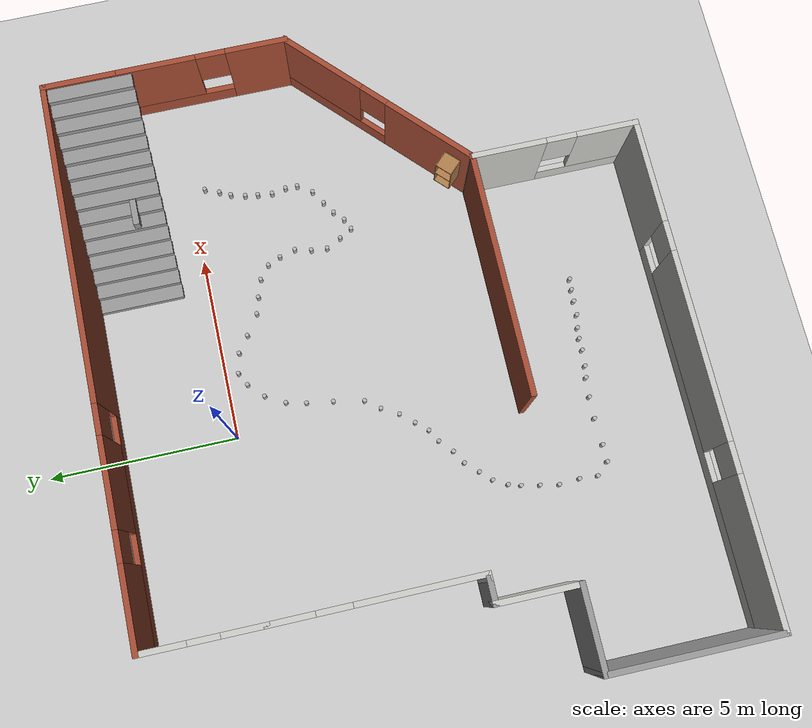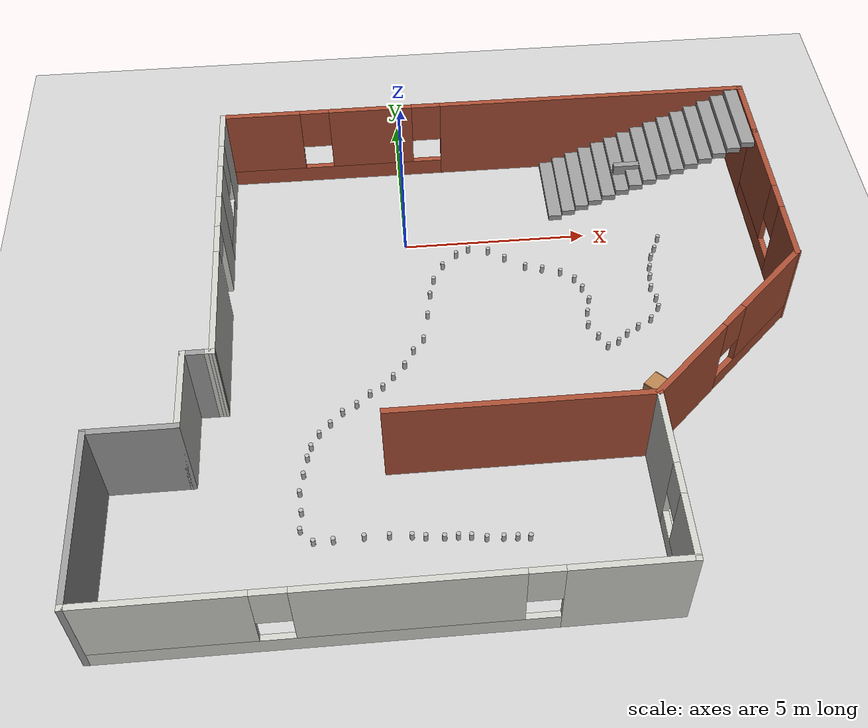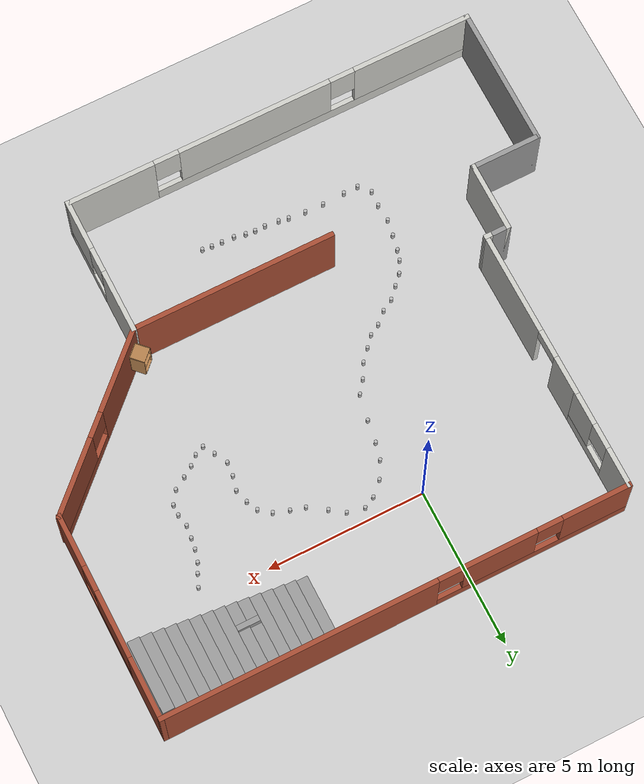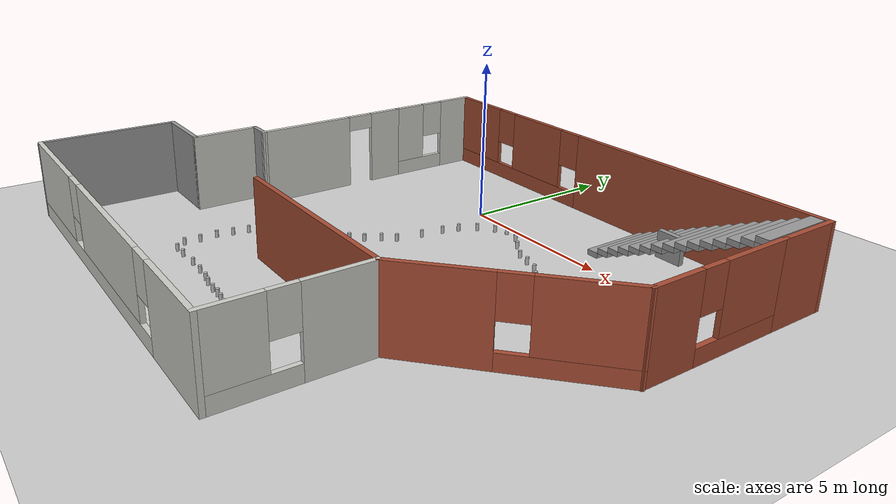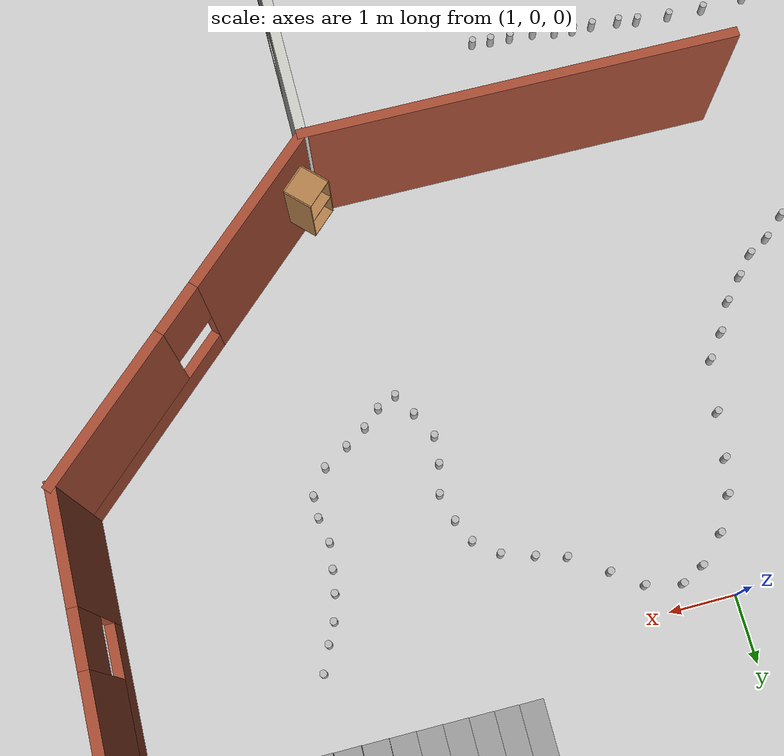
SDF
<sdf version="1.7">
 <world name="default">
  <light name="sun" type="directional">
   <pose>0 0 10 0 -0 0</pose>
   <diffuse>0.8 0.8 0.8 1</diffuse>
   <specular>0.2 0.2 0.2 1</specular>
   <attenuation>
    <range>1000</range>
    <constant>0.9</constant>
    <linear>0.01</linear>
    <quadratic>0.001</quadratic>
   </attenuation>
   <direction>-0.5 0.1 -0.9</direction>
   <spot><inner_angle>0</inner_angle><outer_angle>0</outer_angle><falloff>0</falloff></spot>
  </light>
  <gravity>0 0 -9.8</gravity>
  <magnetic_field>6e-06 2.3e-05 -4.2e-05</magnetic_field>
  <atmosphere type="adiabatic"/>
  <physics type="ode">
   <max_step_size>0.001</max_step_size>
   <real_time_factor>1</real_time_factor>
   <real_time_update_rate>1000</real_time_update_rate>
  </physics>
  <scene><ambient>0.4 0.4 0.4 1</ambient><background>0.7 0.7 0.7 1</background><shadows>1</shadows></scene>
  <audio><device>default</device></audio>
  <spherical_coordinates>
   <surface_model>EARTH_WGS84</surface_model>
   <latitude_deg>0</latitude_deg>
   <longitude_deg>0</longitude_deg>
   <elevation>0</elevation>
   <heading_deg>0</heading_deg>
  </spherical_coordinates>
  <model name="some_house">
   <pose>1.0882 -4.40068 0 0 -0 0</pose>
   <link name="Stairs_1">
    <visual name="Stairs_1_Visual_0">
     <pose>3.20774 6.21774 0.083333 0 -0 1.5708</pose>
     <geometry><box><size>2.24008 0.369439 0.166667</size></box></geometry>
     <material>
      <script><uri>file://media/materials/scripts/gazebo.material</uri><name>Gazebo/Grey</name></script>
      <ambient>1 1 1 1</ambient>
     </material>
     <meta><layer>0</layer></meta>
    </visual>
    <collision name="Stairs_1_Collision_0">
     <geometry><box><size>2.24008 0.369439 0.166667</size></box></geometry>
     <pose>3.20774 6.21774 0.083333 0 -0 1.5708</pose>
    </collision>
    <visual name="Stairs_1_Visual_1">
     <pose>3.57718 6.21774 0.25 0 -0 1.5708</pose>
     <geometry><box><size>2.24008 0.369439 0.166667</size></box></geometry>
     <material>
      <script><uri>file://media/materials/scripts/gazebo.material</uri><name>Gazebo/Grey</name></script>
      <ambient>1 1 1 1</ambient>
     </material>
     <meta><layer>0</layer></meta>
    </visual>
    <collision name="Stairs_1_Collision_1">
     <geometry><box><size>2.24008 0.369439 0.166667</size></box></geometry>
     <pose>3.57718 6.21774 0.25 0 -0 1.5708</pose>
    </collision>
    <visual name="Stairs_1_Visual_2">
     <pose>3.94662 6.21774 0.416667 0 -0 1.5708</pose>
     <geometry><box><size>2.24008 0.369439 0.166667</size></box></geometry>
     <material>
      <script><uri>file://media/materials/scripts/gazebo.material</uri><name>Gazebo/Grey</name></script>
      <ambient>1 1 1 1</ambient>
     </material>
     <meta><layer>0</layer></meta>
    </visual>
    <collision name="Stairs_1_Collision_2">
     <geometry><box><size>2.24008 0.369439 0.166667</size></box></geometry>
     <pose>3.94662 6.21774 0.416667 0 -0 1.5708</pose>
    </collision>
    <visual name="Stairs_1_Visual_3">
     <pose>4.31606 6.21774 0.583333 0 -0 1.5708</pose>
     <geometry><box><size>2.24008 0.369439 0.166667</size></box></geometry>
     <material>
      <script><uri>file://media/materials/scripts/gazebo.material</uri><name>Gazebo/Grey</name></script>
      <ambient>1 1 1 1</ambient>
     </material>
     <meta><layer>0</layer></meta>
    </visual>
    <collision name="Stairs_1_Collision_3">
     <geometry><box><size>2.24008 0.369439 0.166667</size></box></geometry>
     <pose>4.31606 6.21774 0.583333 0 -0 1.5708</pose>
    </collision>
    <visual name="Stairs_1_Visual_4">
     <pose>4.6855 6.21774 0.75 0 -0 1.5708</pose>
     <geometry><box><size>2.24008 0.369439 0.166667</size></box></geometry>
     <material>
      <script><uri>file://media/materials/scripts/gazebo.material</uri><name>Gazebo/Grey</name></script>
      <ambient>1 1 1 1</ambient>
     </material>
     <meta><layer>0</layer></meta>
    </visual>
    <collision name="Stairs_1_Collision_4">
     <geometry><box><size>2.24008 0.369439 0.166667</size></box></geometry>
     <pose>4.6855 6.21774 0.75 0 -0 1.5708</pose>
    </collision>
    <visual name="Stairs_1_Visual_5">
     <pose>5.05494 6.21774 0.916667 0 -0 1.5708</pose>
     <geometry><box><size>2.24008 0.369439 0.166667</size></box></geometry>
     <material>
      <script><uri>file://media/materials/scripts/gazebo.material</uri><name>Gazebo/Grey</name></script>
      <ambient>1 1 1 1</ambient>
     </material>
     <meta><layer>0</layer></meta>
    </visual>
    <collision name="Stairs_1_Collision_5">
     <geometry><box><size>2.24008 0.369439 0.166667</size></box></geometry>
     <pose>5.05494 6.21774 0.916667 0 -0 1.5708</pose>
    </collision>
    <visual name="Stairs_1_Visual_6">
     <pose>5.42438 6.21774 1.08333 0 -0 1.5708</pose>
     <geometry><box><size>2.24008 0.369439 0.166667</size></box></geometry>
     <material>
      <script><uri>file://media/materials/scripts/gazebo.material</uri><name>Gazebo/Grey</name></script>
      <ambient>1 1 1 1</ambient>
     </material>
     <meta><layer>0</layer></meta>
    </visual>
    <collision name="Stairs_1_Collision_6">
     <geometry><box><size>2.24008 0.369439 0.166667</size></box></geometry>
     <pose>5.42438 6.21774 1.08333 0 -0 1.5708</pose>
    </collision>
    <visual name="Stairs_1_Visual_7">
     <pose>5.79382 6.21774 1.25 0 -0 1.5708</pose>
     <geometry><box><size>2.24008 0.369439 0.166667</size></box></geometry>
     <material>
      <script><uri>file://media/materials/scripts/gazebo.material</uri><name>Gazebo/Grey</name></script>
      <ambient>1 1 1 1</ambient>
     </material>
     <meta><layer>0</layer></meta>
    </visual>
    <collision name="Stairs_1_Collision_7">
     <geometry><box><size>2.24008 0.369439 0.166667</size></box></geometry>
     <pose>5.79382 6.21774 1.25 0 -0 1.5708</pose>
    </collision>
    <visual name="Stairs_1_Visual_8">
     <pose>6.16326 6.21774 1.41667 0 -0 1.5708</pose>
     <geometry><box><size>2.24008 0.369439 0.166667</size></box></geometry>
     <material>
      <script><uri>file://media/materials/scripts/gazebo.material</uri><name>Gazebo/Grey</name></script>
      <ambient>1 1 1 1</ambient>
     </material>
     <meta><layer>0</layer></meta>
    </visual>
    <collision name="Stairs_1_Collision_8">
     <geometry><box><size>2.24008 0.369439 0.166667</size></box></geometry>
     <pose>6.16326 6.21774 1.41667 0 -0 1.5708</pose>
    </collision>
    <visual name="Stairs_1_Visual_9">
     <pose>6.5327 6.21774 1.58333 0 -0 1.5708</pose>
     <geometry><box><size>2.24008 0.369439 0.166667</size></box></geometry>
     <material>
      <script><uri>file://media/materials/scripts/gazebo.material</uri><name>Gazebo/Grey</name></script>
      <ambient>1 1 1 1</ambient>
     </material>
     <meta><layer>0</layer></meta>
    </visual>
    <collision name="Stairs_1_Collision_9">
     <geometry><box><size>2.24008 0.369439 0.166667</size></box></geometry>
     <pose>6.5327 6.21774 1.58333 0 -0 1.5708</pose>
    </collision>
    <visual name="Stairs_1_Visual_10">
     <pose>6.90214 6.21774 1.75 0 -0 1.5708</pose>
     <geometry><box><size>2.24008 0.369439 0.166667</size></box></geometry>
     <material>
      <script><uri>file://media/materials/scripts/gazebo.material</uri><name>Gazebo/Grey</name></script>
      <ambient>1 1 1 1</ambient>
     </material>
     <meta><layer>0</layer></meta>
    </visual>
    <collision name="Stairs_1_Collision_10">
     <geometry><box><size>2.24008 0.369439 0.166667</size></box></geometry>
     <pose>6.90214 6.21774 1.75 0 -0 1.5708</pose>
    </collision>
    <visual name="Stairs_1_Visual_11">
     <pose>7.27158 6.21774 1.91667 0 -0 1.5708</pose>
     <geometry><box><size>2.24008 0.369439 0.166667</size></box></geometry>
     <material>
      <script><uri>file://media/materials/scripts/gazebo.material</uri><name>Gazebo/Grey</name></script>
      <ambient>1 1 1 1</ambient>
     </material>
     <meta><layer>0</layer></meta>
    </visual>
    <collision name="Stairs_1_Collision_11">
     <geometry><box><size>2.24008 0.369439 0.166667</size></box></geometry>
     <pose>7.27158 6.21774 1.91667 0 -0 1.5708</pose>
    </collision>
    <visual name="Stairs_1_Visual_12">
     <pose>7.64102 6.21774 2.08333 0 -0 1.5708</pose>
     <geometry><box><size>2.24008 0.369439 0.166667</size></box></geometry>
     <material>
      <script><uri>file://media/materials/scripts/gazebo.material</uri><name>Gazebo/Grey</name></script>
      <ambient>1 1 1 1</ambient>
     </material>
     <meta><layer>0</layer></meta>
    </visual>
    <collision name="Stairs_1_Collision_12">
     <geometry><box><size>2.24008 0.369439 0.166667</size></box></geometry>
     <pose>7.64102 6.21774 2.08333 0 -0 1.5708</pose>
    </collision>
    <visual name="Stairs_1_Visual_13">
     <pose>8.01046 6.21774 2.25 0 -0 1.5708</pose>
     <geometry><box><size>2.24008 0.369439 0.166667</size></box></geometry>
     <material>
      <script><uri>file://media/materials/scripts/gazebo.material</uri><name>Gazebo/Grey</name></script>
      <ambient>1 1 1 1</ambient>
     </material>
     <meta><layer>0</layer></meta>
    </visual>
    <collision name="Stairs_1_Collision_13">
     <geometry><box><size>2.24008 0.369439 0.166667</size></box></geometry>
     <pose>8.01046 6.21774 2.25 0 -0 1.5708</pose>
    </collision>
    <visual name="Stairs_1_Visual_14">
     <pose>8.37989 6.21774 2.41667 0 -0 1.5708</pose>
     <geometry><box><size>2.24008 0.369439 0.166667</size></box></geometry>
     <material>
      <script><uri>file://media/materials/scripts/gazebo.material</uri><name>Gazebo/Grey</name></script>
      <ambient>1 1 1 1</ambient>
     </material>
     <meta><layer>0</layer></meta>
    </visual>
    <collision name="Stairs_1_Collision_14">
     <geometry><box><size>2.24008 0.369439 0.166667</size></box></geometry>
     <pose>8.37989 6.21774 2.41667 0 -0 1.5708</pose>
    </collision>
   </link>
   <link name="Wall_16">
    <pose>6.53448 -1.05 0 0 -0 0.760111</pose>
    <visual name="Wall_16_Visual_0">
     <pose>-1.66 0 1.25 0 -0 0</pose>
     <geometry><box><size>2.73288 0.15 2.5</size></box></geometry>
     <material>
      <script><uri>file://media/materials/scripts/gazebo.material</uri><name>Gazebo/Bricks</name></script>
      <ambient>1 1 1 1</ambient>
     </material>
     <meta><layer>0</layer></meta>
    </visual>
    <collision name="Wall_16_Collision_0">
     <geometry><box><size>2.73288 0.15 2.5</size></box></geometry>
     <pose>-1.66 0 1.25 0 -0 0</pose>
    </collision>
    <visual name="Wall_16_Visual_1">
     <pose>1.36644 0 0.25 0 -0 0</pose>
     <geometry><box><size>3.32001 0.15 0.5</size></box></geometry>
     <material>
      <script><uri>file://media/materials/scripts/gazebo.material</uri><name>Gazebo/Bricks</name></script>
      <ambient>1 1 1 1</ambient>
     </material>
     <meta><layer>0</layer></meta>
    </visual>
    <collision name="Wall_16_Collision_1">
     <geometry><box><size>3.32001 0.15 0.5</size></box></geometry>
     <pose>1.36644 0 0.25 0 -0 0</pose>
    </collision>
    <visual name="Wall_16_Visual_2">
     <pose>1.76644 0 1.5 0 -0 0</pose>
     <geometry><box><size>2.52 0.15 2</size></box></geometry>
     <material>
      <script><uri>file://media/materials/scripts/gazebo.material</uri><name>Gazebo/Bricks</name></script>
      <ambient>1 1 1 1</ambient>
     </material>
     <meta><layer>0</layer></meta>
    </visual>
    <collision name="Wall_16_Collision_2">
     <geometry><box><size>2.52 0.15 2</size></box></geometry>
     <pose>1.76644 0 1.5 0 -0 0</pose>
    </collision>
    <visual name="Wall_16_Visual_3">
     <pose>0.106438 0 1.9 0 -0 0</pose>
     <geometry><box><size>0.8 0.15 1.2</size></box></geometry>
     <material>
      <script><uri>file://media/materials/scripts/gazebo.material</uri><name>Gazebo/Bricks</name></script>
      <ambient>1 1 1 1</ambient>
     </material>
     <meta><layer>0</layer></meta>
    </visual>
    <collision name="Wall_16_Collision_3">
     <geometry><box><size>0.8 0.15 1.2</size></box></geometry>
     <pose>0.106438 0 1.9 0 -0 0</pose>
    </collision>
   </link>
   <link name="Wall_17">
    <pose>8.67357 3.28355 0 0 -0 1.5708</pose>
    <visual name="Wall_17_Visual_0">
     <pose>-1.53185 0 1.25 0 -0 0</pose>
     <geometry><box><size>1.68629 0.15 2.5</size></box></geometry>
     <material>
      <script><uri>file://media/materials/scripts/gazebo.material</uri><name>Gazebo/Bricks</name></script>
      <ambient>1 1 1 1</ambient>
     </material>
     <meta><layer>0</layer></meta>
    </visual>
    <collision name="Wall_17_Collision_0">
     <geometry><box><size>1.68629 0.15 2.5</size></box></geometry>
     <pose>-1.53185 0 1.25 0 -0 0</pose>
    </collision>
    <visual name="Wall_17_Visual_1">
     <pose>0.843146 0 0.25 0 -0 0</pose>
     <geometry><box><size>3.06371 0.15 0.5</size></box></geometry>
     <material>
      <script><uri>file://media/materials/scripts/gazebo.material</uri><name>Gazebo/Bricks</name></script>
      <ambient>1 1 1 1</ambient>
     </material>
     <meta><layer>0</layer></meta>
    </visual>
    <collision name="Wall_17_Collision_1">
     <geometry><box><size>3.06371 0.15 0.5</size></box></geometry>
     <pose>0.843146 0 0.25 0 -0 0</pose>
    </collision>
    <visual name="Wall_17_Visual_2">
     <pose>1.24315 0 1.5 0 -0 0</pose>
     <geometry><box><size>2.26371 0.15 2</size></box></geometry>
     <material>
      <script><uri>file://media/materials/scripts/gazebo.material</uri><name>Gazebo/Bricks</name></script>
      <ambient>1 1 1 1</ambient>
     </material>
     <meta><layer>0</layer></meta>
    </visual>
    <collision name="Wall_17_Collision_2">
     <geometry><box><size>2.26371 0.15 2</size></box></geometry>
     <pose>1.24315 0 1.5 0 -0 0</pose>
    </collision>
    <visual name="Wall_17_Visual_3">
     <pose>-0.288707 0 1.9 0 -0 0</pose>
     <geometry><box><size>0.8 0.15 1.2</size></box></geometry>
     <material>
      <script><uri>file://media/materials/scripts/gazebo.material</uri><name>Gazebo/Bricks</name></script>
      <ambient>1 1 1 1</ambient>
     </material>
     <meta><layer>0</layer></meta>
    </visual>
    <collision name="Wall_17_Collision_3">
     <geometry><box><size>0.8 0.15 1.2</size></box></geometry>
     <pose>-0.288707 0 1.9 0 -0 0</pose>
    </collision>
   </link>
   <link name="Wall_18">
    <collision name="Wall_18_Collision">
     <geometry><box><size>2 0.15 2.5</size></box></geometry>
     <pose>0 0 1.25 0 -0 0</pose>
    </collision>
    <visual name="Wall_18_Visual">
     <pose>0 0 1.25 0 -0 0</pose>
     <geometry><box><size>2 0.15 2.5</size></box></geometry>
     <material>
      <script><uri>file://media/materials/scripts/gazebo.material</uri><name>Gazebo/Bricks</name></script>
      <ambient>1 1 1 1</ambient>
     </material>
     <meta><layer>0</layer></meta>
    </visual>
    <pose>8.67357 6.50855 0 0 -0 1.5708</pose>
   </link>
   <link name="Wall_19">
    <pose>1.37357 7.43355 0 0 -0 3.14159</pose>
    <visual name="Wall_19_Visual_0">
     <pose>-3.05953 0 1.25 0 -0 0</pose>
     <geometry><box><size>8.63094 0.15 2.5</size></box></geometry>
     <material>
      <script><uri>file://media/materials/scripts/gazebo.material</uri><name>Gazebo/Bricks</name></script>
      <ambient>1 1 1 1</ambient>
     </material>
     <meta><layer>0</layer></meta>
    </visual>
    <collision name="Wall_19_Collision_0">
     <geometry><box><size>8.63094 0.15 2.5</size></box></geometry>
     <pose>-3.05953 0 1.25 0 -0 0</pose>
    </collision>
    <visual name="Wall_19_Visual_1">
     <pose>4.31547 0 0.25 0 -0 0</pose>
     <geometry><box><size>6.11906 0.15 0.5</size></box></geometry>
     <material>
      <script><uri>file://media/materials/scripts/gazebo.material</uri><name>Gazebo/Bricks</name></script>
      <ambient>1 1 1 1</ambient>
     </material>
     <meta><layer>0</layer></meta>
    </visual>
    <collision name="Wall_19_Collision_1">
     <geometry><box><size>6.11906 0.15 0.5</size></box></geometry>
     <pose>4.31547 0 0.25 0 -0 0</pose>
    </collision>
    <visual name="Wall_19_Visual_2">
     <pose>3.21359 0 1.5 0 -0 0</pose>
     <geometry><box><size>2.31531 0.15 2</size></box></geometry>
     <material>
      <script><uri>file://media/materials/scripts/gazebo.material</uri><name>Gazebo/Bricks</name></script>
      <ambient>1 1 1 1</ambient>
     </material>
     <meta><layer>0</layer></meta>
    </visual>
    <collision name="Wall_19_Collision_2">
     <geometry><box><size>2.31531 0.15 2</size></box></geometry>
     <pose>3.21359 0 1.5 0 -0 0</pose>
    </collision>
    <visual name="Wall_19_Visual_3">
     <pose>6.27312 0 1.5 0 -0 0</pose>
     <geometry><box><size>2.20375 0.15 2</size></box></geometry>
     <material>
      <script><uri>file://media/materials/scripts/gazebo.material</uri><name>Gazebo/Bricks</name></script>
      <ambient>1 1 1 1</ambient>
     </material>
     <meta><layer>0</layer></meta>
    </visual>
    <collision name="Wall_19_Collision_3">
     <geometry><box><size>2.20375 0.15 2</size></box></geometry>
     <pose>6.27312 0 1.5 0 -0 0</pose>
    </collision>
    <visual name="Wall_19_Visual_4">
     <pose>1.65594 0 1.9 0 -0 0</pose>
     <geometry><box><size>0.8 0.15 1.2</size></box></geometry>
     <material>
      <script><uri>file://media/materials/scripts/gazebo.material</uri><name>Gazebo/Bricks</name></script>
      <ambient>1 1 1 1</ambient>
     </material>
     <meta><layer>0</layer></meta>
    </visual>
    <collision name="Wall_19_Collision_4">
     <geometry><box><size>0.8 0.15 1.2</size></box></geometry>
     <pose>1.65594 0 1.9 0 -0 0</pose>
    </collision>
    <visual name="Wall_19_Visual_5">
     <pose>4.77125 0 1.9 0 -0 0</pose>
     <geometry><box><size>0.8 0.15 1.2</size></box></geometry>
     <material>
      <script><uri>file://media/materials/scripts/gazebo.material</uri><name>Gazebo/Bricks</name></script>
      <ambient>1 1 1 1</ambient>
     </material>
     <meta><layer>0</layer></meta>
    </visual>
    <collision name="Wall_19_Collision_5">
     <geometry><box><size>0.8 0.15 1.2</size></box></geometry>
     <pose>4.77125 0 1.9 0 -0 0</pose>
    </collision>
   </link>
   <link name="Wall_20">
    <pose>-5.92643 5.88355 0 0 -0 -1.5708</pose>
    <visual name="Wall_20_Visual_0">
     <pose>-0.984754 0 1.25 0 -0 0</pose>
     <geometry><box><size>1.28049 0.15 2.5</size></box></geometry>
     <material>
      <script><uri>file://media/materials/scripts/gazebo.material</uri><name>Gazebo/CeilingTiled</name></script>
      <ambient>0.921569 0.807843 0.615686 1</ambient>
     </material>
     <meta><layer>0</layer></meta>
    </visual>
    <collision name="Wall_20_Collision_0">
     <geometry><box><size>1.28049 0.15 2.5</size></box></geometry>
     <pose>-0.984754 0 1.25 0 -0 0</pose>
    </collision>
    <visual name="Wall_20_Visual_1">
     <pose>0.640246 0 0.25 0 -0 0</pose>
     <geometry><box><size>1.96951 0.15 0.5</size></box></geometry>
     <material>
      <script><uri>file://media/materials/scripts/gazebo.material</uri><name>Gazebo/CeilingTiled</name></script>
      <ambient>0.921569 0.807843 0.615686 1</ambient>
     </material>
     <meta><layer>0</layer></meta>
    </visual>
    <collision name="Wall_20_Collision_1">
     <geometry><box><size>1.96951 0.15 0.5</size></box></geometry>
     <pose>0.640246 0 0.25 0 -0 0</pose>
    </collision>
    <visual name="Wall_20_Visual_2">
     <pose>1.04025 0 1.5 0 -0 0</pose>
     <geometry><box><size>1.16951 0.15 2</size></box></geometry>
     <material>
      <script><uri>file://media/materials/scripts/gazebo.material</uri><name>Gazebo/CeilingTiled</name></script>
      <ambient>0.921569 0.807843 0.615686 1</ambient>
     </material>
     <meta><layer>0</layer></meta>
    </visual>
    <collision name="Wall_20_Collision_2">
     <geometry><box><size>1.16951 0.15 2</size></box></geometry>
     <pose>1.04025 0 1.5 0 -0 0</pose>
    </collision>
    <visual name="Wall_20_Visual_3">
     <pose>0.055492 0 1.9 0 -0 0</pose>
     <geometry><box><size>0.8 0.15 1.2</size></box></geometry>
     <material>
      <script><uri>file://media/materials/scripts/gazebo.material</uri><name>Gazebo/CeilingTiled</name></script>
      <ambient>0.921569 0.807843 0.615686 1</ambient>
     </material>
     <meta><layer>0</layer></meta>
    </visual>
    <collision name="Wall_20_Collision_3">
     <geometry><box><size>0.8 0.15 1.2</size></box></geometry>
     <pose>0.055492 0 1.9 0 -0 0</pose>
    </collision>
   </link>
   <link name="Wall_25">
    <collision name="Wall_25_Collision">
     <geometry><box><size>6.5 0.15 2.5</size></box></geometry>
     <pose>0 0 1.25 0 -0 0</pose>
    </collision>
    <visual name="Wall_25_Visual">
     <pose>0 0 1.25 0 -0 0</pose>
     <geometry><box><size>6.5 0.15 2.5</size></box></geometry>
     <material>
      <script><uri>file://media/materials/scripts/gazebo.material</uri><name>Gazebo/Bricks</name></script>
      <ambient>1 1 1 1</ambient>
     </material>
     <meta><layer>0</layer></meta>
    </visual>
    <pose>1.2204 -3.08355 0 0 -0 3.14159</pose>
   </link>
   <link name="Wall_32">
    <pose>4.3954 -5.25855 0 0 -0 -1.5708</pose>
    <visual name="Wall_32_Visual_0">
     <pose>-1.22831 0 1.25 0 -0 0</pose>
     <geometry><box><size>2.04338 0.15 2.5</size></box></geometry>
     <material>
      <script><uri>file://media/materials/scripts/gazebo.material</uri><name>Gazebo/CeilingTiled</name></script>
      <ambient>1 1 1 1</ambient>
     </material>
     <meta><layer>0</layer></meta>
    </visual>
    <collision name="Wall_32_Collision_0">
     <geometry><box><size>2.04338 0.15 2.5</size></box></geometry>
     <pose>-1.22831 0 1.25 0 -0 0</pose>
    </collision>
    <visual name="Wall_32_Visual_1">
     <pose>1.02169 0 0.25 0 -0 0</pose>
     <geometry><box><size>2.45662 0.15 0.5</size></box></geometry>
     <material>
      <script><uri>file://media/materials/scripts/gazebo.material</uri><name>Gazebo/CeilingTiled</name></script>
      <ambient>1 1 1 1</ambient>
     </material>
     <meta><layer>0</layer></meta>
    </visual>
    <collision name="Wall_32_Collision_1">
     <geometry><box><size>2.45662 0.15 0.5</size></box></geometry>
     <pose>1.02169 0 0.25 0 -0 0</pose>
    </collision>
    <visual name="Wall_32_Visual_2">
     <pose>1.42169 0 1.5 0 -0 0</pose>
     <geometry><box><size>1.65661 0.15 2</size></box></geometry>
     <material>
      <script><uri>file://media/materials/scripts/gazebo.material</uri><name>Gazebo/CeilingTiled</name></script>
      <ambient>1 1 1 1</ambient>
     </material>
     <meta><layer>0</layer></meta>
    </visual>
    <collision name="Wall_32_Collision_2">
     <geometry><box><size>1.65661 0.15 2</size></box></geometry>
     <pose>1.42169 0 1.5 0 -0 0</pose>
    </collision>
    <visual name="Wall_32_Visual_3">
     <pose>0.193385 0 1.9 0 -0 0</pose>
     <geometry><box><size>0.8 0.15 1.2</size></box></geometry>
     <material>
      <script><uri>file://media/materials/scripts/gazebo.material</uri><name>Gazebo/CeilingTiled</name></script>
      <ambient>1 1 1 1</ambient>
     </material>
     <meta><layer>0</layer></meta>
    </visual>
    <collision name="Wall_32_Collision_3">
     <geometry><box><size>0.8 0.15 1.2</size></box></geometry>
     <pose>0.193385 0 1.9 0 -0 0</pose>
    </collision>
   </link>
   <link name="Wall_33">
    <pose>-2.1546 -7.43355 0 0 -0 3.14159</pose>
    <visual name="Wall_33_Visual_0">
     <pose>-5.20373 0 1.25 0 -0 0</pose>
     <geometry><box><size>2.84254 0.15 2.5</size></box></geometry>
     <material>
      <script><uri>file://media/materials/scripts/gazebo.material</uri><name>Gazebo/CeilingTiled</name></script>
      <ambient>1 1 1 1</ambient>
     </material>
     <meta><layer>0</layer></meta>
    </visual>
    <collision name="Wall_33_Collision_0">
     <geometry><box><size>2.84254 0.15 2.5</size></box></geometry>
     <pose>-5.20373 0 1.25 0 -0 0</pose>
    </collision>
    <visual name="Wall_33_Visual_1">
     <pose>1.42127 0 0.25 0 -0 0</pose>
     <geometry><box><size>10.4075 0.15 0.5</size></box></geometry>
     <material>
      <script><uri>file://media/materials/scripts/gazebo.material</uri><name>Gazebo/CeilingTiled</name></script>
      <ambient>1 1 1 1</ambient>
     </material>
     <meta><layer>0</layer></meta>
    </visual>
    <collision name="Wall_33_Collision_1">
     <geometry><box><size>10.4075 0.15 0.5</size></box></geometry>
     <pose>1.42127 0 0.25 0 -0 0</pose>
    </collision>
    <visual name="Wall_33_Visual_2">
     <pose>-0.506978 0 1.5 0 -0 0</pose>
     <geometry><box><size>4.95096 0.15 2</size></box></geometry>
     <material>
      <script><uri>file://media/materials/scripts/gazebo.material</uri><name>Gazebo/CeilingTiled</name></script>
      <ambient>1 1 1 1</ambient>
     </material>
     <meta><layer>0</layer></meta>
    </visual>
    <collision name="Wall_33_Collision_2">
     <geometry><box><size>4.95096 0.15 2</size></box></geometry>
     <pose>-0.506978 0 1.5 0 -0 0</pose>
    </collision>
    <visual name="Wall_33_Visual_3">
     <pose>4.69675 0 1.5 0 -0 0</pose>
     <geometry><box><size>3.8565 0.15 2</size></box></geometry>
     <material>
      <script><uri>file://media/materials/scripts/gazebo.material</uri><name>Gazebo/CeilingTiled</name></script>
      <ambient>1 1 1 1</ambient>
     </material>
     <meta><layer>0</layer></meta>
    </visual>
    <collision name="Wall_33_Collision_3">
     <geometry><box><size>3.8565 0.15 2</size></box></geometry>
     <pose>4.69675 0 1.5 0 -0 0</pose>
    </collision>
    <visual name="Wall_33_Visual_4">
     <pose>-3.38246 0 1.9 0 -0 0</pose>
     <geometry><box><size>0.8 0.15 1.2</size></box></geometry>
     <material>
      <script><uri>file://media/materials/scripts/gazebo.material</uri><name>Gazebo/CeilingTiled</name></script>
      <ambient>1 1 1 1</ambient>
     </material>
     <meta><layer>0</layer></meta>
    </visual>
    <collision name="Wall_33_Collision_4">
     <geometry><box><size>0.8 0.15 1.2</size></box></geometry>
     <pose>-3.38246 0 1.9 0 -0 0</pose>
    </collision>
    <visual name="Wall_33_Visual_5">
     <pose>2.3685 0 1.9 0 -0 0</pose>
     <geometry><box><size>0.8 0.15 1.2</size></box></geometry>
     <material>
      <script><uri>file://media/materials/scripts/gazebo.material</uri><name>Gazebo/CeilingTiled</name></script>
      <ambient>1 1 1 1</ambient>
     </material>
     <meta><layer>0</layer></meta>
    </visual>
    <collision name="Wall_33_Collision_5">
     <geometry><box><size>0.8 0.15 1.2</size></box></geometry>
     <pose>2.3685 0 1.9 0 -0 0</pose>
    </collision>
   </link>
   <link name="Wall_34">
    <collision name="Wall_34_Collision">
     <geometry><box><size>4.5 0.15 2.5</size></box></geometry>
     <pose>0 0 1.25 0 -0 0</pose>
    </collision>
    <visual name="Wall_34_Visual">
     <pose>0 0 1.25 0 -0 0</pose>
     <geometry><box><size>4.5 0.15 2.5</size></box></geometry>
     <material>
      <script><uri>file://media/materials/scripts/gazebo.material</uri><name>Gazebo/Grey</name></script>
      <ambient>1 1 1 1</ambient>
     </material>
     <meta><layer>0</layer></meta>
    </visual>
    <pose>-8.7046 -5.25855 0 0 -0 1.5708</pose>
   </link>
   <link name="Wall_35">
    <collision name="Wall_35_Collision">
     <geometry><box><size>2.25 0.15 2.5</size></box></geometry>
     <pose>0 0 1.25 0 -0 0</pose>
    </collision>
    <visual name="Wall_35_Visual">
     <pose>0 0 1.25 0 -0 0</pose>
     <geometry><box><size>2.25 0.15 2.5</size></box></geometry>
     <material>
      <script><uri>file://media/materials/scripts/gazebo.material</uri><name>Gazebo/Grey</name></script>
      <ambient>1 1 1 1</ambient>
     </material>
     <meta><layer>0</layer></meta>
    </visual>
    <pose>-7.6546 -3.08355 0 0 -0 0</pose>
   </link>
   <link name="Wall_36">
    <collision name="Wall_36_Collision">
     <geometry><box><size>2.25 0.15 2.5</size></box></geometry>
     <pose>0 0 1.25 0 -0 0</pose>
    </collision>
    <visual name="Wall_36_Visual">
     <pose>0 0 1.25 0 -0 0</pose>
     <geometry><box><size>2.25 0.15 2.5</size></box></geometry>
     <material>
      <script><uri>file://media/materials/scripts/gazebo.material</uri><name>Gazebo/CeilingTiled</name></script>
      <ambient>0.921569 0.807843 0.615686 1</ambient>
     </material>
     <meta><layer>0</layer></meta>
    </visual>
    <pose>-6.6046 -2.03355 0 0 -0 1.5708</pose>
   </link>
   <link name="Wall_37">
    <collision name="Wall_37_Collision">
     <geometry><box><size>0.75 0.15 2.5</size></box></geometry>
     <pose>0 0 1.25 0 -0 0</pose>
    </collision>
    <visual name="Wall_37_Visual">
     <pose>0 0 1.25 0 -0 0</pose>
     <geometry><box><size>0.75 0.15 2.5</size></box></geometry>
     <material>
      <script><uri>file://media/materials/scripts/gazebo.material</uri><name>Gazebo/Grey</name></script>
      <ambient>1 1 1 1</ambient>
     </material>
     <meta><layer>0</layer></meta>
    </visual>
    <pose>-6.3046 -0.98355 0 0 -0 0</pose>
   </link>
   <link name="Wall_39">
    <collision name="Wall_39_Collision">
     <geometry><box><size>0.25 0.15 2.5</size></box></geometry>
     <pose>0 0 1.25 0 -0 0</pose>
    </collision>
    <visual name="Wall_39_Visual">
     <pose>0 0 1.25 0 -0 0</pose>
     <geometry><box><size>0.25 0.15 2.5</size></box></geometry>
     <material>
      <script><uri>file://media/materials/scripts/gazebo.material</uri><name>Gazebo/CeilingTiled</name></script>
      <ambient>0.921569 0.807843 0.615686 1</ambient>
     </material>
     <meta><layer>0</layer></meta>
    </visual>
    <pose>-5.9546 -0.98355 0 0 -0 0</pose>
   </link>
   <link name="Wall_40">
    <pose>-5.91552 1.675 0 0 -0 1.5749</pose>
    <visual name="Wall_40_Visual_0">
     <pose>-1.0692 0 1.25 0 -0 0</pose>
     <geometry><box><size>3.32875 0.15 2.5</size></box></geometry>
     <material>
      <script><uri>file://media/materials/scripts/gazebo.material</uri><name>Gazebo/CeilingTiled</name></script>
      <ambient>0.921569 0.807843 0.615686 1</ambient>
     </material>
     <meta><layer>0</layer></meta>
    </visual>
    <collision name="Wall_40_Collision_0">
     <geometry><box><size>3.32875 0.15 2.5</size></box></geometry>
     <pose>-1.0692 0 1.25 0 -0 0</pose>
    </collision>
    <visual name="Wall_40_Visual_1">
     <pose>2.11438 0 1.25 0 -0 0</pose>
     <geometry><box><size>1.23839 0.15 2.5</size></box></geometry>
     <material>
      <script><uri>file://media/materials/scripts/gazebo.material</uri><name>Gazebo/CeilingTiled</name></script>
      <ambient>0.921569 0.807843 0.615686 1</ambient>
     </material>
     <meta><layer>0</layer></meta>
    </visual>
    <collision name="Wall_40_Collision_1">
     <geometry><box><size>1.23839 0.15 2.5</size></box></geometry>
     <pose>2.11438 0 1.25 0 -0 0</pose>
    </collision>
    <visual name="Wall_40_Visual_2">
     <pose>1.04518 0 2.25 0 -0 0</pose>
     <geometry><box><size>0.9 0.15 0.5</size></box></geometry>
     <material>
      <script><uri>file://media/materials/scripts/gazebo.material</uri><name>Gazebo/CeilingTiled</name></script>
      <ambient>0.921569 0.807843 0.615686 1</ambient>
     </material>
     <meta><layer>0</layer></meta>
    </visual>
    <collision name="Wall_40_Collision_2">
     <geometry><box><size>0.9 0.15 0.5</size></box></geometry>
     <pose>1.04518 0 2.25 0 -0 0</pose>
    </collision>
   </link>
   <link name="Window_14">
    <collision name="Window_14_Collision">
     <geometry><box><size>0.8 0.17 0.8</size></box></geometry>
     <pose>0 0 0.4 0 -0 0</pose>
    </collision>
    <visual name="Window_14_Visual">
     <pose>0 0 0.4 0 -0 0</pose>
     <geometry><box><size>0.8 0.17 0.8</size></box></geometry>
     <material>
      <script><uri>file://media/materials/scripts/gazebo.material</uri><name>Gazebo/Grey</name></script>
     </material>
    </visual>
    <pose>5.29819 5.84106 0.5 0 -0 0</pose>
   </link>
   <static>1</static>
  </model>
  <model name="cabinet">
   <static>1</static>
   <link name="cabinet_bottom_plate">
    <inertial>
     <pose>0 0 -1 0 -0 0</pose>
     <inertia><ixx>2.05</ixx><ixy>0</ixy><ixz>0</ixz><iyy>2.05</iyy><iyz>0</iyz><izz>2.05</izz></inertia>
     <mass>25</mass>
    </inertial>
    <collision name="cabinet_bottom_plate_geom">
     <pose>0 0 0.01 0 -0 0</pose>
     <geometry><box><size>0.45 0.45 0.02</size></box></geometry>
    </collision>
    <visual name="cabinet_bottom_plate_geom_visual">
     <pose>0 0 0.01 0 -0 0</pose>
     <geometry><box><size>0.45 0.45 0.02</size></box></geometry>
     <material>
      <script><uri>file://media/materials/scripts/gazebo.material</uri><name>Gazebo/Wood</name></script>
     </material>
    </visual>
    <collision name="cabinet_bottom_plate_geom_cabinet_back_plate">
     <pose>0.235 0 0.51 0 -0 0</pose>
     <geometry><box><size>0.02 0.45 1.02</size></box></geometry>
    </collision>
    <visual name="cabinet_bottom_plate_geom_cabinet_back_plate_visual">
     <pose>0.235 0 0.51 0 -0 0</pose>
     <geometry><box><size>0.02 0.45 1.02</size></box></geometry>
     <material>
      <script><uri>file://media/materials/scripts/gazebo.material</uri><name>Gazebo/Wood</name></script>
     </material>
    </visual>
    <collision name="cabinet_bottom_plate_geom_cabinet_left_plate">
     <pose>0 0.235 0.51 0 -0 0</pose>
     <geometry><box><size>0.45 0.02 1.02</size></box></geometry>
    </collision>
    <visual name="cabinet_bottom_plate_geom_cabinet_left_plate_visual">
     <pose>0 0.235 0.51 0 -0 0</pose>
     <geometry><box><size>0.45 0.02 1.02</size></box></geometry>
     <material>
      <script><uri>file://media/materials/scripts/gazebo.material</uri><name>Gazebo/Wood</name></script>
     </material>
    </visual>
    <collision name="cabinet_bottom_plate_geom_cabinet_middle_plate">
     <pose>0 0 0.51 0 -0 0</pose>
     <geometry><box><size>0.45 0.45 0.02</size></box></geometry>
    </collision>
    <visual name="cabinet_bottom_plate_geom_cabinet_middle_plate_visual">
     <pose>0 0 0.51 0 -0 0</pose>
     <geometry><box><size>0.45 0.45 0.02</size></box></geometry>
     <material>
      <script><uri>file://media/materials/scripts/gazebo.material</uri><name>Gazebo/Wood</name></script>
     </material>
    </visual>
    <collision name="cabinet_bottom_plate_geom_cabinet_right_plate">
     <pose>0 -0.235 0.51 0 -0 0</pose>
     <geometry><box><size>0.45 0.02 1.02</size></box></geometry>
    </collision>
    <visual name="cabinet_bottom_plate_geom_cabinet_right_plate_visual">
     <pose>0 -0.235 0.51 0 -0 0</pose>
     <geometry><box><size>0.45 0.02 1.02</size></box></geometry>
     <material>
      <script><uri>file://media/materials/scripts/gazebo.material</uri><name>Gazebo/Wood</name></script>
     </material>
    </visual>
    <collision name="cabinet_bottom_plate_geom_cabinet_top_plate">
     <pose>0 0 1.01 0 -0 0</pose>
     <geometry><box><size>0.45 0.45 0.02</size></box></geometry>
    </collision>
    <visual name="cabinet_bottom_plate_geom_cabinet_top_plate_visual">
     <pose>0 0 1.01 0 -0 0</pose>
     <geometry><box><size>0.45 0.45 0.02</size></box></geometry>
     <material>
      <script><uri>file://media/materials/scripts/gazebo.material</uri><name>Gazebo/Wood</name></script>
     </material>
    </visual>
   </link>
   <pose>5.5953 -6.89266 1.02917 0 0 -0.801525</pose>
  </model>
  <model name="ground_plane">
   <static>1</static>
   <link name="link">
    <collision name="collision">
     <geometry><plane><normal>0 0 1</normal><size>100 100</size></plane></geometry>
     <surface>
      <contact><collide_bitmask>65535</collide_bitmask></contact>
      <friction><ode><mu>100</mu><mu2>50</mu2></ode></friction>
     </surface>
    </collision>
    <visual name="visual">
     <cast_shadows>0</cast_shadows>
     <geometry><plane><normal>0 0 1</normal><size>100 100</size></plane></geometry>
     <material>
      <script><uri>file://media/materials/scripts/gazebo.material</uri><name>Gazebo/Grey</name></script>
     </material>
    </visual>
   </link>
  </model>
  <model name="beer">
   <link name="link">
    <pose>0 0 0.115 0 -0 0</pose>
    <inertial>
     <mass>0.39</mass>
     <inertia><ixx>0.00058</ixx><ixy>0</ixy><ixz>0</ixz><iyy>0.00058</iyy><iyz>0</iyz><izz>0.00019</izz></inertia>
    </inertial>
    <collision name="collision">
     <geometry><cylinder><radius>0.055</radius><length>0.23</length></cylinder></geometry>
    </collision>
    <visual name="visual">
     <geometry><cylinder><radius>0.055</radius><length>0.23</length></cylinder></geometry>
     <material>
      <script>
       <uri>model://beer/materials/scripts</uri>
       <uri>model://beer/materials/textures</uri>
       <name>Beer/Diffuse</name>
      </script>
     </material>
    </visual>
   </link>
   <pose>3.21261 -1.13627 0 0 -0 0</pose>
  </model>
  <model name="beer_clone">
   <link name="link">
    <pose>0 0 0.115 0 -0 0</pose>
    <inertial>
     <mass>0.39</mass>
     <inertia><ixx>0.00058</ixx><ixy>0</ixy><ixz>0</ixz><iyy>0.00058</iyy><iyz>0</iyz><izz>0.00019</izz></inertia>
    </inertial>
    <collision name="collision">
     <geometry><cylinder><radius>0.055</radius><length>0.23</length></cylinder></geometry>
    </collision>
    <visual name="visual">
     <geometry><cylinder><radius>0.055</radius><length>0.23</length></cylinder></geometry>
     <material>
      <script>
       <uri>model://beer/materials/scripts</uri>
       <uri>model://beer/materials/textures</uri>
       <name>Beer/Diffuse</name>
      </script>
     </material>
    </visual>
   </link>
   <pose>3.66049 -1.26777 0 0 -0 0</pose>
  </model>
  <model name="beer_clone_0">
   <link name="link">
    <pose>0 0 0.115 0 -0 0</pose>
    <inertial>
     <mass>0.39</mass>
     <inertia><ixx>0.00058</ixx><ixy>0</ixy><ixz>0</ixz><iyy>0.00058</iyy><iyz>0</iyz><izz>0.00019</izz></inertia>
    </inertial>
    <collision name="collision">
     <geometry><cylinder><radius>0.055</radius><length>0.23</length></cylinder></geometry>
    </collision>
    <visual name="visual">
     <geometry><cylinder><radius>0.055</radius><length>0.23</length></cylinder></geometry>
     <material>
      <script>
       <uri>model://beer/materials/scripts</uri>
       <uri>model://beer/materials/textures</uri>
       <name>Beer/Diffuse</name>
      </script>
     </material>
    </visual>
   </link>
   <pose>4.13975 -1.42824 0 0 -0 0</pose>
  </model>
  <model name="beer_clone_1">
   <link name="link">
    <pose>0 0 0.115 0 -0 0</pose>
    <inertial>
     <mass>0.39</mass>
     <inertia><ixx>0.00058</ixx><ixy>0</ixy><ixz>0</ixz><iyy>0.00058</iyy><iyz>0</iyz><izz>0.00019</izz></inertia>
    </inertial>
    <collision name="collision">
     <geometry><cylinder><radius>0.055</radius><length>0.23</length></cylinder></geometry>
    </collision>
    <visual name="visual">
     <geometry><cylinder><radius>0.055</radius><length>0.23</length></cylinder></geometry>
     <material>
      <script>
       <uri>model://beer/materials/scripts</uri>
       <uri>model://beer/materials/textures</uri>
       <name>Beer/Diffuse</name>
      </script>
     </material>
    </visual>
   </link>
   <pose>4.49238 -1.70706 0 0 -0 0</pose>
  </model>
  <model name="beer_clone_2">
   <link name="link">
    <pose>0 0 0.115 0 -0 0</pose>
    <inertial>
     <mass>0.39</mass>
     <inertia><ixx>0.00058</ixx><ixy>0</ixy><ixz>0</ixz><iyy>0.00058</iyy><iyz>0</iyz><izz>0.00019</izz></inertia>
    </inertial>
    <collision name="collision">
     <geometry><cylinder><radius>0.055</radius><length>0.23</length></cylinder></geometry>
    </collision>
    <visual name="visual">
     <geometry><cylinder><radius>0.055</radius><length>0.23</length></cylinder></geometry>
     <material>
      <script>
       <uri>model://beer/materials/scripts</uri>
       <uri>model://beer/materials/textures</uri>
       <name>Beer/Diffuse</name>
      </script>
     </material>
    </visual>
   </link>
   <pose>4.65567 -2.06316 0 0 -0 0</pose>
  </model>
  <model name="beer_clone_3">
   <link name="link">
    <pose>0 0 0.115 0 -0 0</pose>
    <inertial>
     <mass>0.39</mass>
     <inertia><ixx>0.00058</ixx><ixy>0</ixy><ixz>0</ixz><iyy>0.00058</iyy><iyz>0</iyz><izz>0.00019</izz></inertia>
    </inertial>
    <collision name="collision">
     <geometry><cylinder><radius>0.055</radius><length>0.23</length></cylinder></geometry>
    </collision>
    <visual name="visual">
     <geometry><cylinder><radius>0.055</radius><length>0.23</length></cylinder></geometry>
     <material>
      <script>
       <uri>model://beer/materials/scripts</uri>
       <uri>model://beer/materials/textures</uri>
       <name>Beer/Diffuse</name>
      </script>
     </material>
    </visual>
   </link>
   <pose>4.77323 -2.50039 0 0 -0 0</pose>
  </model>
  <model name="beer_clone_4">
   <link name="link">
    <pose>0 0 0.115 0 -0 0</pose>
    <inertial>
     <mass>0.39</mass>
     <inertia><ixx>0.00058</ixx><ixy>0</ixy><ixz>0</ixz><iyy>0.00058</iyy><iyz>0</iyz><izz>0.00019</izz></inertia>
    </inertial>
    <collision name="collision">
     <geometry><cylinder><radius>0.055</radius><length>0.23</length></cylinder></geometry>
    </collision>
    <visual name="visual">
     <geometry><cylinder><radius>0.055</radius><length>0.23</length></cylinder></geometry>
     <material>
      <script>
       <uri>model://beer/materials/scripts</uri>
       <uri>model://beer/materials/textures</uri>
       <name>Beer/Diffuse</name>
      </script>
     </material>
    </visual>
   </link>
   <pose>4.6645 -2.9432 0 0 -0 0</pose>
  </model>
  <model name="beer_clone_5">
   <link name="link">
    <pose>0 0 0.115 0 -0 0</pose>
    <inertial>
     <mass>0.39</mass>
     <inertia><ixx>0.00058</ixx><ixy>0</ixy><ixz>0</ixz><iyy>0.00058</iyy><iyz>0</iyz><izz>0.00019</izz></inertia>
    </inertial>
    <collision name="collision">
     <geometry><cylinder><radius>0.055</radius><length>0.23</length></cylinder></geometry>
    </collision>
    <visual name="visual">
     <geometry><cylinder><radius>0.055</radius><length>0.23</length></cylinder></geometry>
     <material>
      <script>
       <uri>model://beer/materials/scripts</uri>
       <uri>model://beer/materials/textures</uri>
       <name>Beer/Diffuse</name>
      </script>
     </material>
    </visual>
   </link>
   <pose>4.6236 -3.37544 0 0 -0 0</pose>
  </model>
  <model name="beer_clone_6">
   <link name="link">
    <pose>0 0 0.115 0 -0 0</pose>
    <inertial>
     <mass>0.39</mass>
     <inertia><ixx>0.00058</ixx><ixy>0</ixy><ixz>0</ixz><iyy>0.00058</iyy><iyz>0</iyz><izz>0.00019</izz></inertia>
    </inertial>
    <collision name="collision">
     <geometry><cylinder><radius>0.055</radius><length>0.23</length></cylinder></geometry>
    </collision>
    <visual name="visual">
     <geometry><cylinder><radius>0.055</radius><length>0.23</length></cylinder></geometry>
     <material>
      <script>
       <uri>model://beer/materials/scripts</uri>
       <uri>model://beer/materials/textures</uri>
       <name>Beer/Diffuse</name>
      </script>
     </material>
    </visual>
   </link>
   <pose>4.83288 -3.78668 0 0 -0 0</pose>
  </model>
  <model name="beer_clone_7">
   <link name="link">
    <pose>0 0 0.115 0 -0 0</pose>
    <inertial>
     <mass>0.39</mass>
     <inertia><ixx>0.00058</ixx><ixy>0</ixy><ixz>0</ixz><iyy>0.00058</iyy><iyz>0</iyz><izz>0.00019</izz></inertia>
    </inertial>
    <collision name="collision">
     <geometry><cylinder><radius>0.055</radius><length>0.23</length></cylinder></geometry>
    </collision>
    <visual name="visual">
     <geometry><cylinder><radius>0.055</radius><length>0.23</length></cylinder></geometry>
     <material>
      <script>
       <uri>model://beer/materials/scripts</uri>
       <uri>model://beer/materials/textures</uri>
       <name>Beer/Diffuse</name>
      </script>
     </material>
    </visual>
   </link>
   <pose>5.03652 -4.13206 0 0 -0 0</pose>
  </model>
  <model name="beer_clone_8">
   <link name="link">
    <pose>0 0 0.115 0 -0 0</pose>
    <inertial>
     <mass>0.39</mass>
     <inertia><ixx>0.00058</ixx><ixy>0</ixy><ixz>0</ixz><iyy>0.00058</iyy><iyz>0</iyz><izz>0.00019</izz></inertia>
    </inertial>
    <collision name="collision">
     <geometry><cylinder><radius>0.055</radius><length>0.23</length></cylinder></geometry>
    </collision>
    <visual name="visual">
     <geometry><cylinder><radius>0.055</radius><length>0.23</length></cylinder></geometry>
     <material>
      <script>
       <uri>model://beer/materials/scripts</uri>
       <uri>model://beer/materials/textures</uri>
       <name>Beer/Diffuse</name>
      </script>
     </material>
    </visual>
   </link>
   <pose>5.33528 -4.00424 0 0 -0 0</pose>
  </model>
  <model name="beer_clone_9">
   <link name="link">
    <pose>0 0 0.115 0 -0 0</pose>
    <inertial>
     <mass>0.39</mass>
     <inertia><ixx>0.00058</ixx><ixy>0</ixy><ixz>0</ixz><iyy>0.00058</iyy><iyz>0</iyz><izz>0.00019</izz></inertia>
    </inertial>
    <collision name="collision">
     <geometry><cylinder><radius>0.055</radius><length>0.23</length></cylinder></geometry>
    </collision>
    <visual name="visual">
     <geometry><cylinder><radius>0.055</radius><length>0.23</length></cylinder></geometry>
     <material>
      <script>
       <uri>model://beer/materials/scripts</uri>
       <uri>model://beer/materials/textures</uri>
       <name>Beer/Diffuse</name>
      </script>
     </material>
    </visual>
   </link>
   <pose>5.60126 -3.76155 0 0 -0 0</pose>
  </model>
  <model name="beer_clone_10">
   <link name="link">
    <pose>0 0 0.115 0 -0 0</pose>
    <inertial>
     <mass>0.39</mass>
     <inertia><ixx>0.00058</ixx><ixy>0</ixy><ixz>0</ixz><iyy>0.00058</iyy><iyz>0</iyz><izz>0.00019</izz></inertia>
    </inertial>
    <collision name="collision">
     <geometry><cylinder><radius>0.055</radius><length>0.23</length></cylinder></geometry>
    </collision>
    <visual name="visual">
     <geometry><cylinder><radius>0.055</radius><length>0.23</length></cylinder></geometry>
     <material>
      <script>
       <uri>model://beer/materials/scripts</uri>
       <uri>model://beer/materials/textures</uri>
       <name>Beer/Diffuse</name>
      </script>
     </material>
    </visual>
   </link>
   <pose>5.92957 -3.54976 0 0 -0 0</pose>
  </model>
  <model name="beer_clone_11">
   <link name="link">
    <pose>0 0 0.115 0 -0 0</pose>
    <inertial>
     <mass>0.39</mass>
     <inertia><ixx>0.00058</ixx><ixy>0</ixy><ixz>0</ixz><iyy>0.00058</iyy><iyz>0</iyz><izz>0.00019</izz></inertia>
    </inertial>
    <collision name="collision">
     <geometry><cylinder><radius>0.055</radius><length>0.23</length></cylinder></geometry>
    </collision>
    <visual name="visual">
     <geometry><cylinder><radius>0.055</radius><length>0.23</length></cylinder></geometry>
     <material>
      <script>
       <uri>model://beer/materials/scripts</uri>
       <uri>model://beer/materials/textures</uri>
       <name>Beer/Diffuse</name>
      </script>
     </material>
    </visual>
   </link>
   <pose>6.31289 -3.31554 0 0 -0 0</pose>
  </model>
  <model name="beer_clone_12">
   <link name="link">
    <pose>0 0 0.115 0 -0 0</pose>
    <inertial>
     <mass>0.39</mass>
     <inertia><ixx>0.00058</ixx><ixy>0</ixy><ixz>0</ixz><iyy>0.00058</iyy><iyz>0</iyz><izz>0.00019</izz></inertia>
    </inertial>
    <collision name="collision">
     <geometry><cylinder><radius>0.055</radius><length>0.23</length></cylinder></geometry>
    </collision>
    <visual name="visual">
     <geometry><cylinder><radius>0.055</radius><length>0.23</length></cylinder></geometry>
     <material>
      <script>
       <uri>model://beer/materials/scripts</uri>
       <uri>model://beer/materials/textures</uri>
       <name>Beer/Diffuse</name>
      </script>
     </material>
    </visual>
   </link>
   <pose>6.57749 -2.93491 0 0 -0 0</pose>
  </model>
  <model name="beer_clone_13">
   <link name="link">
    <pose>0 0 0.115 0 -0 0</pose>
    <inertial>
     <mass>0.39</mass>
     <inertia><ixx>0.00058</ixx><ixy>0</ixy><ixz>0</ixz><iyy>0.00058</iyy><iyz>0</iyz><izz>0.00019</izz></inertia>
    </inertial>
    <collision name="collision">
     <geometry><cylinder><radius>0.055</radius><length>0.23</length></cylinder></geometry>
    </collision>
    <visual name="visual">
     <geometry><cylinder><radius>0.055</radius><length>0.23</length></cylinder></geometry>
     <material>
      <script>
       <uri>model://beer/materials/scripts</uri>
       <uri>model://beer/materials/textures</uri>
       <name>Beer/Diffuse</name>
      </script>
     </material>
    </visual>
   </link>
   <pose>6.58421 -2.60151 0 0 -0 0</pose>
  </model>
  <model name="beer_clone_14">
   <link name="link">
    <pose>0 0 0.115 0 -0 0</pose>
    <inertial>
     <mass>0.39</mass>
     <inertia><ixx>0.00058</ixx><ixy>0</ixy><ixz>0</ixz><iyy>0.00058</iyy><iyz>0</iyz><izz>0.00019</izz></inertia>
    </inertial>
    <collision name="collision">
     <geometry><cylinder><radius>0.055</radius><length>0.23</length></cylinder></geometry>
    </collision>
    <visual name="visual">
     <geometry><cylinder><radius>0.055</radius><length>0.23</length></cylinder></geometry>
     <material>
      <script>
       <uri>model://beer/materials/scripts</uri>
       <uri>model://beer/materials/textures</uri>
       <name>Beer/Diffuse</name>
      </script>
     </material>
    </visual>
   </link>
   <pose>6.51125 -2.20879 0 0 -0 0</pose>
  </model>
  <model name="beer_clone_15">
   <link name="link">
    <pose>0 0 0.115 0 -0 0</pose>
    <inertial>
     <mass>0.39</mass>
     <inertia><ixx>0.00058</ixx><ixy>0</ixy><ixz>0</ixz><iyy>0.00058</iyy><iyz>0</iyz><izz>0.00019</izz></inertia>
    </inertial>
    <collision name="collision">
     <geometry><cylinder><radius>0.055</radius><length>0.23</length></cylinder></geometry>
    </collision>
    <visual name="visual">
     <geometry><cylinder><radius>0.055</radius><length>0.23</length></cylinder></geometry>
     <material>
      <script>
       <uri>model://beer/materials/scripts</uri>
       <uri>model://beer/materials/textures</uri>
       <name>Beer/Diffuse</name>
      </script>
     </material>
    </visual>
   </link>
   <pose>6.5567 -1.81592 0 0 -0 0</pose>
  </model>
  <model name="beer_clone_16">
   <link name="link">
    <pose>0 0 0.115 0 -0 0</pose>
    <inertial>
     <mass>0.39</mass>
     <inertia><ixx>0.00058</ixx><ixy>0</ixy><ixz>0</ixz><iyy>0.00058</iyy><iyz>0</iyz><izz>0.00019</izz></inertia>
    </inertial>
    <collision name="collision">
     <geometry><cylinder><radius>0.055</radius><length>0.23</length></cylinder></geometry>
    </collision>
    <visual name="visual">
     <geometry><cylinder><radius>0.055</radius><length>0.23</length></cylinder></geometry>
     <material>
      <script>
       <uri>model://beer/materials/scripts</uri>
       <uri>model://beer/materials/textures</uri>
       <name>Beer/Diffuse</name>
      </script>
     </material>
    </visual>
   </link>
   <pose>6.60844 -1.46873 0 0 -0 0</pose>
  </model>
  <model name="beer_clone_17">
   <link name="link">
    <pose>0 0 0.115 0 -0 0</pose>
    <inertial>
     <mass>0.39</mass>
     <inertia><ixx>0.00058</ixx><ixy>0</ixy><ixz>0</ixz><iyy>0.00058</iyy><iyz>0</iyz><izz>0.00019</izz></inertia>
    </inertial>
    <collision name="collision">
     <geometry><cylinder><radius>0.055</radius><length>0.23</length></cylinder></geometry>
    </collision>
    <visual name="visual">
     <geometry><cylinder><radius>0.055</radius><length>0.23</length></cylinder></geometry>
     <material>
      <script>
       <uri>model://beer/materials/scripts</uri>
       <uri>model://beer/materials/textures</uri>
       <name>Beer/Diffuse</name>
      </script>
     </material>
    </visual>
   </link>
   <pose>6.71563 -1.08294 0 0 -0 0</pose>
  </model>
  <model name="beer_clone_18">
   <link name="link">
    <pose>0 0 0.115 0 -0 0</pose>
    <inertial>
     <mass>0.39</mass>
     <inertia><ixx>0.00058</ixx><ixy>0</ixy><ixz>0</ixz><iyy>0.00058</iyy><iyz>0</iyz><izz>0.00019</izz></inertia>
    </inertial>
    <collision name="collision">
     <geometry><cylinder><radius>0.055</radius><length>0.23</length></cylinder></geometry>
    </collision>
    <visual name="visual">
     <geometry><cylinder><radius>0.055</radius><length>0.23</length></cylinder></geometry>
     <material>
      <script>
       <uri>model://beer/materials/scripts</uri>
       <uri>model://beer/materials/textures</uri>
       <name>Beer/Diffuse</name>
      </script>
     </material>
    </visual>
   </link>
   <pose>6.8616 -0.788139 0 0 -0 0</pose>
  </model>
  <model name="beer_clone_19">
   <link name="link">
    <pose>0 0 0.115 0 -0 0</pose>
    <inertial>
     <mass>0.39</mass>
     <inertia><ixx>0.00058</ixx><ixy>0</ixy><ixz>0</ixz><iyy>0.00058</iyy><iyz>0</iyz><izz>0.00019</izz></inertia>
    </inertial>
    <collision name="collision">
     <geometry><cylinder><radius>0.055</radius><length>0.23</length></cylinder></geometry>
    </collision>
    <visual name="visual">
     <geometry><cylinder><radius>0.055</radius><length>0.23</length></cylinder></geometry>
     <material>
      <script>
       <uri>model://beer/materials/scripts</uri>
       <uri>model://beer/materials/textures</uri>
       <name>Beer/Diffuse</name>
      </script>
     </material>
    </visual>
   </link>
   <pose>7.02593 -0.406793 0 0 -0 0</pose>
  </model>
  <model name="beer_clone_20">
   <link name="link">
    <pose>0 0 0.115 0 -0 0</pose>
    <inertial>
     <mass>0.39</mass>
     <inertia><ixx>0.00058</ixx><ixy>0</ixy><ixz>0</ixz><iyy>0.00058</iyy><iyz>0</iyz><izz>0.00019</izz></inertia>
    </inertial>
    <collision name="collision">
     <geometry><cylinder><radius>0.055</radius><length>0.23</length></cylinder></geometry>
    </collision>
    <visual name="visual">
     <geometry><cylinder><radius>0.055</radius><length>0.23</length></cylinder></geometry>
     <material>
      <script>
       <uri>model://beer/materials/scripts</uri>
       <uri>model://beer/materials/textures</uri>
       <name>Beer/Diffuse</name>
      </script>
     </material>
    </visual>
   </link>
   <pose>2.67407 -0.77334 0 0 -0 0</pose>
  </model>
  <model name="beer_clone_21">
   <link name="link">
    <pose>0 0 0.115 0 -0 0</pose>
    <inertial>
     <mass>0.39</mass>
     <inertia><ixx>0.00058</ixx><ixy>0</ixy><ixz>0</ixz><iyy>0.00058</iyy><iyz>0</iyz><izz>0.00019</izz></inertia>
    </inertial>
    <collision name="collision">
     <geometry><cylinder><radius>0.055</radius><length>0.23</length></cylinder></geometry>
    </collision>
    <visual name="visual">
     <geometry><cylinder><radius>0.055</radius><length>0.23</length></cylinder></geometry>
     <material>
      <script>
       <uri>model://beer/materials/scripts</uri>
       <uri>model://beer/materials/textures</uri>
       <name>Beer/Diffuse</name>
      </script>
     </material>
    </visual>
   </link>
   <pose>2.24285 -0.463914 0 0 -0 0</pose>
  </model>
  <model name="beer_clone_22">
   <link name="link">
    <pose>0 0 0.115 0 -0 0</pose>
    <inertial>
     <mass>0.39</mass>
     <inertia><ixx>0.00058</ixx><ixy>0</ixy><ixz>0</ixz><iyy>0.00058</iyy><iyz>0</iyz><izz>0.00019</izz></inertia>
    </inertial>
    <collision name="collision">
     <geometry><cylinder><radius>0.055</radius><length>0.23</length></cylinder></geometry>
    </collision>
    <visual name="visual">
     <geometry><cylinder><radius>0.055</radius><length>0.23</length></cylinder></geometry>
     <material>
      <script>
       <uri>model://beer/materials/scripts</uri>
       <uri>model://beer/materials/textures</uri>
       <name>Beer/Diffuse</name>
      </script>
     </material>
    </visual>
   </link>
   <pose>1.702 -0.345969 0 0 -0 0</pose>
  </model>
  <model name="beer_clone_23">
   <link name="link">
    <pose>0 0 0.115 0 -0 0</pose>
    <inertial>
     <mass>0.39</mass>
     <inertia><ixx>0.00058</ixx><ixy>0</ixy><ixz>0</ixz><iyy>0.00058</iyy><iyz>0</iyz><izz>0.00019</izz></inertia>
    </inertial>
    <collision name="collision">
     <geometry><cylinder><radius>0.055</radius><length>0.23</length></cylinder></geometry>
    </collision>
    <visual name="visual">
     <geometry><cylinder><radius>0.055</radius><length>0.23</length></cylinder></geometry>
     <material>
      <script>
       <uri>model://beer/materials/scripts</uri>
       <uri>model://beer/materials/textures</uri>
       <name>Beer/Diffuse</name>
      </script>
     </material>
    </visual>
   </link>
   <pose>1.34989 -0.523721 0 0 -0 0</pose>
  </model>
  <model name="beer_clone_24">
   <link name="link">
    <pose>0 0 0.115 0 -0 0</pose>
    <inertial>
     <mass>0.39</mass>
     <inertia><ixx>0.00058</ixx><ixy>0</ixy><ixz>0</ixz><iyy>0.00058</iyy><iyz>0</iyz><izz>0.00019</izz></inertia>
    </inertial>
    <collision name="collision">
     <geometry><cylinder><radius>0.055</radius><length>0.23</length></cylinder></geometry>
    </collision>
    <visual name="visual">
     <geometry><cylinder><radius>0.055</radius><length>0.23</length></cylinder></geometry>
     <material>
      <script>
       <uri>model://beer/materials/scripts</uri>
       <uri>model://beer/materials/textures</uri>
       <name>Beer/Diffuse</name>
      </script>
     </material>
    </visual>
   </link>
   <pose>0.948589 -0.908925 0 0 -0 0</pose>
  </model>
  <model name="beer_clone_25">
   <link name="link">
    <pose>0 0 0.115 0 -0 0</pose>
    <inertial>
     <mass>0.39</mass>
     <inertia><ixx>0.00058</ixx><ixy>0</ixy><ixz>0</ixz><iyy>0.00058</iyy><iyz>0</iyz><izz>0.00019</izz></inertia>
    </inertial>
    <collision name="collision">
     <geometry><cylinder><radius>0.055</radius><length>0.23</length></cylinder></geometry>
    </collision>
    <visual name="visual">
     <geometry><cylinder><radius>0.055</radius><length>0.23</length></cylinder></geometry>
     <material>
      <script>
       <uri>model://beer/materials/scripts</uri>
       <uri>model://beer/materials/textures</uri>
       <name>Beer/Diffuse</name>
      </script>
     </material>
    </visual>
   </link>
   <pose>0.658754 -1.42656 0 0 -0 0</pose>
  </model>
  <model name="beer_clone_26">
   <link name="link">
    <pose>0 0 0.115 0 -0 0</pose>
    <inertial>
     <mass>0.39</mass>
     <inertia><ixx>0.00058</ixx><ixy>0</ixy><ixz>0</ixz><iyy>0.00058</iyy><iyz>0</iyz><izz>0.00019</izz></inertia>
    </inertial>
    <collision name="collision">
     <geometry><cylinder><radius>0.055</radius><length>0.23</length></cylinder></geometry>
    </collision>
    <visual name="visual">
     <geometry><cylinder><radius>0.055</radius><length>0.23</length></cylinder></geometry>
     <material>
      <script>
       <uri>model://beer/materials/scripts</uri>
       <uri>model://beer/materials/textures</uri>
       <name>Beer/Diffuse</name>
      </script>
     </material>
    </visual>
   </link>
   <pose>0.528178 -1.95725 0 0 -0 0</pose>
  </model>
  <model name="beer_clone_27">
   <link name="link">
    <pose>0 0 0.115 0 -0 0</pose>
    <inertial>
     <mass>0.39</mass>
     <inertia><ixx>0.00058</ixx><ixy>0</ixy><ixz>0</ixz><iyy>0.00058</iyy><iyz>0</iyz><izz>0.00019</izz></inertia>
    </inertial>
    <collision name="collision">
     <geometry><cylinder><radius>0.055</radius><length>0.23</length></cylinder></geometry>
    </collision>
    <visual name="visual">
     <geometry><cylinder><radius>0.055</radius><length>0.23</length></cylinder></geometry>
     <material>
      <script>
       <uri>model://beer/materials/scripts</uri>
       <uri>model://beer/materials/textures</uri>
       <name>Beer/Diffuse</name>
      </script>
     </material>
    </visual>
   </link>
   <pose>0.418289 -2.66152 0 0 -0 0</pose>
  </model>
  <model name="beer_clone_28">
   <link name="link">
    <pose>0 0 0.115 0 -0 0</pose>
    <inertial>
     <mass>0.39</mass>
     <inertia><ixx>0.00058</ixx><ixy>0</ixy><ixz>0</ixz><iyy>0.00058</iyy><iyz>0</iyz><izz>0.00019</izz></inertia>
    </inertial>
    <collision name="collision">
     <geometry><cylinder><radius>0.055</radius><length>0.23</length></cylinder></geometry>
    </collision>
    <visual name="visual">
     <geometry><cylinder><radius>0.055</radius><length>0.23</length></cylinder></geometry>
     <material>
      <script>
       <uri>model://beer/materials/scripts</uri>
       <uri>model://beer/materials/textures</uri>
       <name>Beer/Diffuse</name>
      </script>
     </material>
    </visual>
   </link>
   <pose>0.253525 -3.47533 0 0 -0 0</pose>
  </model>
  <model name="beer_clone_29">
   <link name="link">
    <pose>0 0 0.115 0 -0 0</pose>
    <inertial>
     <mass>0.39</mass>
     <inertia><ixx>0.00058</ixx><ixy>0</ixy><ixz>0</ixz><iyy>0.00058</iyy><iyz>0</iyz><izz>0.00019</izz></inertia>
    </inertial>
    <collision name="collision">
     <geometry><cylinder><radius>0.055</radius><length>0.23</length></cylinder></geometry>
    </collision>
    <visual name="visual">
     <geometry><cylinder><radius>0.055</radius><length>0.23</length></cylinder></geometry>
     <material>
      <script>
       <uri>model://beer/materials/scripts</uri>
       <uri>model://beer/materials/textures</uri>
       <name>Beer/Diffuse</name>
      </script>
     </material>
    </visual>
   </link>
   <pose>-0.034325 -3.85133 0 0 -0 0</pose>
  </model>
  <model name="beer_clone_30">
   <link name="link">
    <pose>0 0 0.115 0 -0 0</pose>
    <inertial>
     <mass>0.39</mass>
     <inertia><ixx>0.00058</ixx><ixy>0</ixy><ixz>0</ixz><iyy>0.00058</iyy><iyz>0</iyz><izz>0.00019</izz></inertia>
    </inertial>
    <collision name="collision">
     <geometry><cylinder><radius>0.055</radius><length>0.23</length></cylinder></geometry>
    </collision>
    <visual name="visual">
     <geometry><cylinder><radius>0.055</radius><length>0.23</length></cylinder></geometry>
     <material>
      <script>
       <uri>model://beer/materials/scripts</uri>
       <uri>model://beer/materials/textures</uri>
       <name>Beer/Diffuse</name>
      </script>
     </material>
    </visual>
   </link>
   <pose>-0.289593 -4.30093 0 0 -0 0</pose>
  </model>
  <model name="beer_clone_31">
   <link name="link">
    <pose>0 0 0.115 0 -0 0</pose>
    <inertial>
     <mass>0.39</mass>
     <inertia><ixx>0.00058</ixx><ixy>0</ixy><ixz>0</ixz><iyy>0.00058</iyy><iyz>0</iyz><izz>0.00019</izz></inertia>
    </inertial>
    <collision name="collision">
     <geometry><cylinder><radius>0.055</radius><length>0.23</length></cylinder></geometry>
    </collision>
    <visual name="visual">
     <geometry><cylinder><radius>0.055</radius><length>0.23</length></cylinder></geometry>
     <material>
      <script>
       <uri>model://beer/materials/scripts</uri>
       <uri>model://beer/materials/textures</uri>
       <name>Beer/Diffuse</name>
      </script>
     </material>
    </visual>
   </link>
   <pose>-0.602273 -4.65243 0 0 -0 0</pose>
  </model>
  <model name="beer_clone_32">
   <link name="link">
    <pose>0 0 0.115 0 -0 0</pose>
    <inertial>
     <mass>0.39</mass>
     <inertia><ixx>0.00058</ixx><ixy>0</ixy><ixz>0</ixz><iyy>0.00058</iyy><iyz>0</iyz><izz>0.00019</izz></inertia>
    </inertial>
    <collision name="collision">
     <geometry><cylinder><radius>0.055</radius><length>0.23</length></cylinder></geometry>
    </collision>
    <visual name="visual">
     <geometry><cylinder><radius>0.055</radius><length>0.23</length></cylinder></geometry>
     <material>
      <script>
       <uri>model://beer/materials/scripts</uri>
       <uri>model://beer/materials/textures</uri>
       <name>Beer/Diffuse</name>
      </script>
     </material>
    </visual>
   </link>
   <pose>-0.881178 -4.96485 0 0 -0 0</pose>
  </model>
  <model name="beer_clone_33">
   <link name="link">
    <pose>0 0 0.115 0 -0 0</pose>
    <inertial>
     <mass>0.39</mass>
     <inertia><ixx>0.00058</ixx><ixy>0</ixy><ixz>0</ixz><iyy>0.00058</iyy><iyz>0</iyz><izz>0.00019</izz></inertia>
    </inertial>
    <collision name="collision">
     <geometry><cylinder><radius>0.055</radius><length>0.23</length></cylinder></geometry>
    </collision>
    <visual name="visual">
     <geometry><cylinder><radius>0.055</radius><length>0.23</length></cylinder></geometry>
     <material>
      <script>
       <uri>model://beer/materials/scripts</uri>
       <uri>model://beer/materials/textures</uri>
       <name>Beer/Diffuse</name>
      </script>
     </material>
    </visual>
   </link>
   <pose>-1.21469 -5.15361 0 0 -0 0</pose>
  </model>
  <model name="beer_clone_34">
   <link name="link">
    <pose>0 0 0.115 0 -0 0</pose>
    <inertial>
     <mass>0.39</mass>
     <inertia><ixx>0.00058</ixx><ixy>0</ixy><ixz>0</ixz><iyy>0.00058</iyy><iyz>0</iyz><izz>0.00019</izz></inertia>
    </inertial>
    <collision name="collision">
     <geometry><cylinder><radius>0.055</radius><length>0.23</length></cylinder></geometry>
    </collision>
    <visual name="visual">
     <geometry><cylinder><radius>0.055</radius><length>0.23</length></cylinder></geometry>
     <material>
      <script>
       <uri>model://beer/materials/scripts</uri>
       <uri>model://beer/materials/textures</uri>
       <name>Beer/Diffuse</name>
      </script>
     </material>
    </visual>
   </link>
   <pose>-1.56116 -5.46531 0 0 -0 0</pose>
  </model>
  <model name="beer_clone_35">
   <link name="link">
    <pose>0 0 0.115 0 -0 0</pose>
    <inertial>
     <mass>0.39</mass>
     <inertia><ixx>0.00058</ixx><ixy>0</ixy><ixz>0</ixz><iyy>0.00058</iyy><iyz>0</iyz><izz>0.00019</izz></inertia>
    </inertial>
    <collision name="collision">
     <geometry><cylinder><radius>0.055</radius><length>0.23</length></cylinder></geometry>
    </collision>
    <visual name="visual">
     <geometry><cylinder><radius>0.055</radius><length>0.23</length></cylinder></geometry>
     <material>
      <script>
       <uri>model://beer/materials/scripts</uri>
       <uri>model://beer/materials/textures</uri>
       <name>Beer/Diffuse</name>
      </script>
     </material>
    </visual>
   </link>
   <pose>-1.92078 -5.67655 0 0 -0 0</pose>
  </model>
  <model name="beer_clone_36">
   <link name="link">
    <pose>0 0 0.115 0 -0 0</pose>
    <inertial>
     <mass>0.39</mass>
     <inertia><ixx>0.00058</ixx><ixy>0</ixy><ixz>0</ixz><iyy>0.00058</iyy><iyz>0</iyz><izz>0.00019</izz></inertia>
    </inertial>
    <collision name="collision">
     <geometry><cylinder><radius>0.055</radius><length>0.23</length></cylinder></geometry>
    </collision>
    <visual name="visual">
     <geometry><cylinder><radius>0.055</radius><length>0.23</length></cylinder></geometry>
     <material>
      <script>
       <uri>model://beer/materials/scripts</uri>
       <uri>model://beer/materials/textures</uri>
       <name>Beer/Diffuse</name>
      </script>
     </material>
    </visual>
   </link>
   <pose>-2.23229 -6.00202 0 0 -0 0</pose>
  </model>
  <model name="beer_clone_37">
   <link name="link">
    <pose>0 0 0.115 0 -0 0</pose>
    <inertial>
     <mass>0.39</mass>
     <inertia><ixx>0.00058</ixx><ixy>0</ixy><ixz>0</ixz><iyy>0.00058</iyy><iyz>0</iyz><izz>0.00019</izz></inertia>
    </inertial>
    <collision name="collision">
     <geometry><cylinder><radius>0.055</radius><length>0.23</length></cylinder></geometry>
    </collision>
    <visual name="visual">
     <geometry><cylinder><radius>0.055</radius><length>0.23</length></cylinder></geometry>
     <material>
      <script>
       <uri>model://beer/materials/scripts</uri>
       <uri>model://beer/materials/textures</uri>
       <name>Beer/Diffuse</name>
      </script>
     </material>
    </visual>
   </link>
   <pose>-2.51298 -6.2958 0 0 -0 0</pose>
  </model>
  <model name="beer_clone_38">
   <link name="link">
    <pose>0 0 0.115 0 -0 0</pose>
    <inertial>
     <mass>0.39</mass>
     <inertia><ixx>0.00058</ixx><ixy>0</ixy><ixz>0</ixz><iyy>0.00058</iyy><iyz>0</iyz><izz>0.00019</izz></inertia>
    </inertial>
    <collision name="collision">
     <geometry><cylinder><radius>0.055</radius><length>0.23</length></cylinder></geometry>
    </collision>
    <visual name="visual">
     <geometry><cylinder><radius>0.055</radius><length>0.23</length></cylinder></geometry>
     <material>
      <script>
       <uri>model://beer/materials/scripts</uri>
       <uri>model://beer/materials/textures</uri>
       <name>Beer/Diffuse</name>
      </script>
     </material>
    </visual>
   </link>
   <pose>-2.71569 -6.65942 0 0 -0 0</pose>
  </model>
  <model name="beer_clone_39">
   <link name="link">
    <pose>0 0 0.115 0 -0 0</pose>
    <inertial>
     <mass>0.39</mass>
     <inertia><ixx>0.00058</ixx><ixy>0</ixy><ixz>0</ixz><iyy>0.00058</iyy><iyz>0</iyz><izz>0.00019</izz></inertia>
    </inertial>
    <collision name="collision">
     <geometry><cylinder><radius>0.055</radius><length>0.23</length></cylinder></geometry>
    </collision>
    <visual name="visual">
     <geometry><cylinder><radius>0.055</radius><length>0.23</length></cylinder></geometry>
     <material>
      <script>
       <uri>model://beer/materials/scripts</uri>
       <uri>model://beer/materials/textures</uri>
       <name>Beer/Diffuse</name>
      </script>
     </material>
    </visual>
   </link>
   <pose>-2.81237 -6.98223 0 0 -0 0</pose>
  </model>
  <model name="beer_clone_40">
   <link name="link">
    <pose>0 0 0.115 0 -0 0</pose>
    <inertial>
     <mass>0.39</mass>
     <inertia><ixx>0.00058</ixx><ixy>0</ixy><ixz>0</ixz><iyy>0.00058</iyy><iyz>0</iyz><izz>0.00019</izz></inertia>
    </inertial>
    <collision name="collision">
     <geometry><cylinder><radius>0.055</radius><length>0.23</length></cylinder></geometry>
    </collision>
    <visual name="visual">
     <geometry><cylinder><radius>0.055</radius><length>0.23</length></cylinder></geometry>
     <material>
      <script>
       <uri>model://beer/materials/scripts</uri>
       <uri>model://beer/materials/textures</uri>
       <name>Beer/Diffuse</name>
      </script>
     </material>
    </visual>
   </link>
   <pose>-2.90852 -7.46349 0 0 -0 0</pose>
  </model>
  <model name="beer_clone_41">
   <link name="link">
    <pose>0 0 0.115 0 -0 0</pose>
    <inertial>
     <mass>0.39</mass>
     <inertia><ixx>0.00058</ixx><ixy>0</ixy><ixz>0</ixz><iyy>0.00058</iyy><iyz>0</iyz><izz>0.00019</izz></inertia>
    </inertial>
    <collision name="collision">
     <geometry><cylinder><radius>0.055</radius><length>0.23</length></cylinder></geometry>
    </collision>
    <visual name="visual">
     <geometry><cylinder><radius>0.055</radius><length>0.23</length></cylinder></geometry>
     <material>
      <script>
       <uri>model://beer/materials/scripts</uri>
       <uri>model://beer/materials/textures</uri>
       <name>Beer/Diffuse</name>
      </script>
     </material>
    </visual>
   </link>
   <pose>-3.00309 -7.96324 0 0 -0 0</pose>
  </model>
  <model name="beer_clone_42">
   <link name="link">
    <pose>0 0 0.115 0 -0 0</pose>
    <inertial>
     <mass>0.39</mass>
     <inertia><ixx>0.00058</ixx><ixy>0</ixy><ixz>0</ixz><iyy>0.00058</iyy><iyz>0</iyz><izz>0.00019</izz></inertia>
    </inertial>
    <collision name="collision">
     <geometry><cylinder><radius>0.055</radius><length>0.23</length></cylinder></geometry>
    </collision>
    <visual name="visual">
     <geometry><cylinder><radius>0.055</radius><length>0.23</length></cylinder></geometry>
     <material>
      <script>
       <uri>model://beer/materials/scripts</uri>
       <uri>model://beer/materials/textures</uri>
       <name>Beer/Diffuse</name>
      </script>
     </material>
    </visual>
   </link>
   <pose>-2.96738 -8.51139 0 0 -0 0</pose>
  </model>
  <model name="beer_clone_43">
   <link name="link">
    <pose>0 0 0.115 0 -0 0</pose>
    <inertial>
     <mass>0.39</mass>
     <inertia><ixx>0.00058</ixx><ixy>0</ixy><ixz>0</ixz><iyy>0.00058</iyy><iyz>0</iyz><izz>0.00019</izz></inertia>
    </inertial>
    <collision name="collision">
     <geometry><cylinder><radius>0.055</radius><length>0.23</length></cylinder></geometry>
    </collision>
    <visual name="visual">
     <geometry><cylinder><radius>0.055</radius><length>0.23</length></cylinder></geometry>
     <material>
      <script>
       <uri>model://beer/materials/scripts</uri>
       <uri>model://beer/materials/textures</uri>
       <name>Beer/Diffuse</name>
      </script>
     </material>
    </visual>
   </link>
   <pose>-3 -9 0 0 -0 0</pose>
  </model>
  <model name="beer_clone_44">
   <link name="link">
    <pose>0 0 0.115 0 -0 0</pose>
    <inertial>
     <mass>0.39</mass>
     <inertia><ixx>0.00058</ixx><ixy>0</ixy><ixz>0</ixz><iyy>0.00058</iyy><iyz>0</iyz><izz>0.00019</izz></inertia>
    </inertial>
    <collision name="collision">
     <geometry><cylinder><radius>0.055</radius><length>0.23</length></cylinder></geometry>
    </collision>
    <visual name="visual">
     <geometry><cylinder><radius>0.055</radius><length>0.23</length></cylinder></geometry>
     <material>
      <script>
       <uri>model://beer/materials/scripts</uri>
       <uri>model://beer/materials/textures</uri>
       <name>Beer/Diffuse</name>
      </script>
     </material>
    </visual>
   </link>
   <pose>-2.69641 -9.33648 0 0 -0 0</pose>
  </model>
  <model name="beer_clone_45">
   <link name="link">
    <pose>0 0 0.115 0 -0 0</pose>
    <inertial>
     <mass>0.39</mass>
     <inertia><ixx>0.00058</ixx><ixy>0</ixy><ixz>0</ixz><iyy>0.00058</iyy><iyz>0</iyz><izz>0.00019</izz></inertia>
    </inertial>
    <collision name="collision">
     <geometry><cylinder><radius>0.055</radius><length>0.23</length></cylinder></geometry>
    </collision>
    <visual name="visual">
     <geometry><cylinder><radius>0.055</radius><length>0.23</length></cylinder></geometry>
     <material>
      <script>
       <uri>model://beer/materials/scripts</uri>
       <uri>model://beer/materials/textures</uri>
       <name>Beer/Diffuse</name>
      </script>
     </material>
    </visual>
   </link>
   <pose>-2.23384 -9.33336 0 0 -0 0</pose>
  </model>
  <model name="beer_clone_46">
   <link name="link">
    <pose>0 0 0.115 0 -0 0</pose>
    <inertial>
     <mass>0.39</mass>
     <inertia><ixx>0.00058</ixx><ixy>0</ixy><ixz>0</ixz><iyy>0.00058</iyy><iyz>0</iyz><izz>0.00019</izz></inertia>
    </inertial>
    <collision name="collision">
     <geometry><cylinder><radius>0.055</radius><length>0.23</length></cylinder></geometry>
    </collision>
    <visual name="visual">
     <geometry><cylinder><radius>0.055</radius><length>0.23</length></cylinder></geometry>
     <material>
      <script>
       <uri>model://beer/materials/scripts</uri>
       <uri>model://beer/materials/textures</uri>
       <name>Beer/Diffuse</name>
      </script>
     </material>
    </visual>
   </link>
   <pose>-1.51755 -9.30422 0 0 -0 0</pose>
  </model>
  <model name="beer_clone_47">
   <link name="link">
    <pose>0 0 0.115 0 -0 0</pose>
    <inertial>
     <mass>0.39</mass>
     <inertia><ixx>0.00058</ixx><ixy>0</ixy><ixz>0</ixz><iyy>0.00058</iyy><iyz>0</iyz><izz>0.00019</izz></inertia>
    </inertial>
    <collision name="collision">
     <geometry><cylinder><radius>0.055</radius><length>0.23</length></cylinder></geometry>
    </collision>
    <visual name="visual">
     <geometry><cylinder><radius>0.055</radius><length>0.23</length></cylinder></geometry>
     <material>
      <script>
       <uri>model://beer/materials/scripts</uri>
       <uri>model://beer/materials/textures</uri>
       <name>Beer/Diffuse</name>
      </script>
     </material>
    </visual>
   </link>
   <pose>-0.933255 -9.32148 0 0 -0 0</pose>
  </model>
  <model name="beer_clone_48">
   <link name="link">
    <pose>0 0 0.115 0 -0 0</pose>
    <inertial>
     <mass>0.39</mass>
     <inertia><ixx>0.00058</ixx><ixy>0</ixy><ixz>0</ixz><iyy>0.00058</iyy><iyz>0</iyz><izz>0.00019</izz></inertia>
    </inertial>
    <collision name="collision">
     <geometry><cylinder><radius>0.055</radius><length>0.23</length></cylinder></geometry>
    </collision>
    <visual name="visual">
     <geometry><cylinder><radius>0.055</radius><length>0.23</length></cylinder></geometry>
     <material>
      <script>
       <uri>model://beer/materials/scripts</uri>
       <uri>model://beer/materials/textures</uri>
       <name>Beer/Diffuse</name>
      </script>
     </material>
    </visual>
   </link>
   <pose>-0.406918 -9.3675 0 0 -0 0</pose>
  </model>
  <model name="beer_clone_49">
   <link name="link">
    <pose>0 0 0.115 0 -0 0</pose>
    <inertial>
     <mass>0.39</mass>
     <inertia><ixx>0.00058</ixx><ixy>0</ixy><ixz>0</ixz><iyy>0.00058</iyy><iyz>0</iyz><izz>0.00019</izz></inertia>
    </inertial>
    <collision name="collision">
     <geometry><cylinder><radius>0.055</radius><length>0.23</length></cylinder></geometry>
    </collision>
    <visual name="visual">
     <geometry><cylinder><radius>0.055</radius><length>0.23</length></cylinder></geometry>
     <material>
      <script>
       <uri>model://beer/materials/scripts</uri>
       <uri>model://beer/materials/textures</uri>
       <name>Beer/Diffuse</name>
      </script>
     </material>
    </visual>
   </link>
   <pose>-0.095067 -9.42507 0 0 -0 0</pose>
  </model>
  <model name="beer_clone_50">
   <link name="link">
    <pose>0 0 0.115 0 -0 0</pose>
    <inertial>
     <mass>0.39</mass>
     <inertia><ixx>0.00058</ixx><ixy>0</ixy><ixz>0</ixz><iyy>0.00058</iyy><iyz>0</iyz><izz>0.00019</izz></inertia>
    </inertial>
    <collision name="collision">
     <geometry><cylinder><radius>0.055</radius><length>0.23</length></cylinder></geometry>
    </collision>
    <visual name="visual">
     <geometry><cylinder><radius>0.055</radius><length>0.23</length></cylinder></geometry>
     <material>
      <script>
       <uri>model://beer/materials/scripts</uri>
       <uri>model://beer/materials/textures</uri>
       <name>Beer/Diffuse</name>
      </script>
     </material>
    </visual>
   </link>
   <pose>0.342245 -9.46557 0 0 -0 0</pose>
  </model>
  <model name="beer_clone_51">
   <link name="link">
    <pose>0 0 0.115 0 -0 0</pose>
    <inertial>
     <mass>0.39</mass>
     <inertia><ixx>0.00058</ixx><ixy>0</ixy><ixz>0</ixz><iyy>0.00058</iyy><iyz>0</iyz><izz>0.00019</izz></inertia>
    </inertial>
    <collision name="collision">
     <geometry><cylinder><radius>0.055</radius><length>0.23</length></cylinder></geometry>
    </collision>
    <visual name="visual">
     <geometry><cylinder><radius>0.055</radius><length>0.23</length></cylinder></geometry>
     <material>
      <script>
       <uri>model://beer/materials/scripts</uri>
       <uri>model://beer/materials/textures</uri>
       <name>Beer/Diffuse</name>
      </script>
     </material>
    </visual>
   </link>
   <pose>0.664366 -9.46299 0 0 -0 0</pose>
  </model>
  <model name="beer_clone_52">
   <link name="link">
    <pose>0 0 0.115 0 -0 0</pose>
    <inertial>
     <mass>0.39</mass>
     <inertia><ixx>0.00058</ixx><ixy>0</ixy><ixz>0</ixz><iyy>0.00058</iyy><iyz>0</iyz><izz>0.00019</izz></inertia>
    </inertial>
    <collision name="collision">
     <geometry><cylinder><radius>0.055</radius><length>0.23</length></cylinder></geometry>
    </collision>
    <visual name="visual">
     <geometry><cylinder><radius>0.055</radius><length>0.23</length></cylinder></geometry>
     <material>
      <script>
       <uri>model://beer/materials/scripts</uri>
       <uri>model://beer/materials/textures</uri>
       <name>Beer/Diffuse</name>
      </script>
     </material>
    </visual>
   </link>
   <pose>0.963714 -9.49859 0 0 -0 0</pose>
  </model>
  <model name="beer_clone_53">
   <link name="link">
    <pose>0 0 0.115 0 -0 0</pose>
    <inertial>
     <mass>0.39</mass>
     <inertia><ixx>0.00058</ixx><ixy>0</ixy><ixz>0</ixz><iyy>0.00058</iyy><iyz>0</iyz><izz>0.00019</izz></inertia>
    </inertial>
    <collision name="collision">
     <geometry><cylinder><radius>0.055</radius><length>0.23</length></cylinder></geometry>
    </collision>
    <visual name="visual">
     <geometry><cylinder><radius>0.055</radius><length>0.23</length></cylinder></geometry>
     <material>
      <script>
       <uri>model://beer/materials/scripts</uri>
       <uri>model://beer/materials/textures</uri>
       <name>Beer/Diffuse</name>
      </script>
     </material>
    </visual>
   </link>
   <pose>1.31811 -9.57035 0 0 -0 0</pose>
  </model>
  <model name="beer_clone_54">
   <link name="link">
    <pose>0 0 0.115 0 -0 0</pose>
    <inertial>
     <mass>0.39</mass>
     <inertia><ixx>0.00058</ixx><ixy>0</ixy><ixz>0</ixz><iyy>0.00058</iyy><iyz>0</iyz><izz>0.00019</izz></inertia>
    </inertial>
    <collision name="collision">
     <geometry><cylinder><radius>0.055</radius><length>0.23</length></cylinder></geometry>
    </collision>
    <visual name="visual">
     <geometry><cylinder><radius>0.055</radius><length>0.23</length></cylinder></geometry>
     <material>
      <script>
       <uri>model://beer/materials/scripts</uri>
       <uri>model://beer/materials/textures</uri>
       <name>Beer/Diffuse</name>
      </script>
     </material>
    </visual>
   </link>
   <pose>1.70632 -9.59089 0 0 -0 0</pose>
  </model>
  <model name="beer_clone_55">
   <link name="link">
    <pose>0 0 0.115 0 -0 0</pose>
    <inertial>
     <mass>0.39</mass>
     <inertia><ixx>0.00058</ixx><ixy>0</ixy><ixz>0</ixz><iyy>0.00058</iyy><iyz>0</iyz><izz>0.00019</izz></inertia>
    </inertial>
    <collision name="collision">
     <geometry><cylinder><radius>0.055</radius><length>0.23</length></cylinder></geometry>
    </collision>
    <visual name="visual">
     <geometry><cylinder><radius>0.055</radius><length>0.23</length></cylinder></geometry>
     <material>
      <script>
       <uri>model://beer/materials/scripts</uri>
       <uri>model://beer/materials/textures</uri>
       <name>Beer/Diffuse</name>
      </script>
     </material>
    </visual>
   </link>
   <pose>2.03007 -9.6096 0 0 -0 0</pose>
  </model>
  <model name="beer_clone_56">
   <link name="link">
    <pose>0 0 0.115 0 -0 0</pose>
    <inertial>
     <mass>0.39</mass>
     <inertia><ixx>0.00058</ixx><ixy>0</ixy><ixz>0</ixz><iyy>0.00058</iyy><iyz>0</iyz><izz>0.00019</izz></inertia>
    </inertial>
    <collision name="collision">
     <geometry><cylinder><radius>0.055</radius><length>0.23</length></cylinder></geometry>
    </collision>
    <visual name="visual">
     <geometry><cylinder><radius>0.055</radius><length>0.23</length></cylinder></geometry>
     <material>
      <script>
       <uri>model://beer/materials/scripts</uri>
       <uri>model://beer/materials/textures</uri>
       <name>Beer/Diffuse</name>
      </script>
     </material>
    </visual>
   </link>
   <pose>2.32994 -9.63857 0 0 -0 0</pose>
  </model>
 </world>
</sdf>
